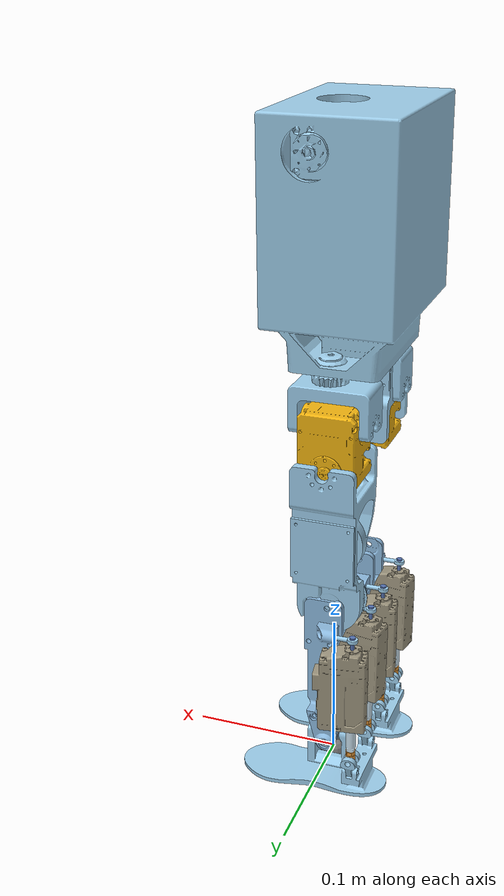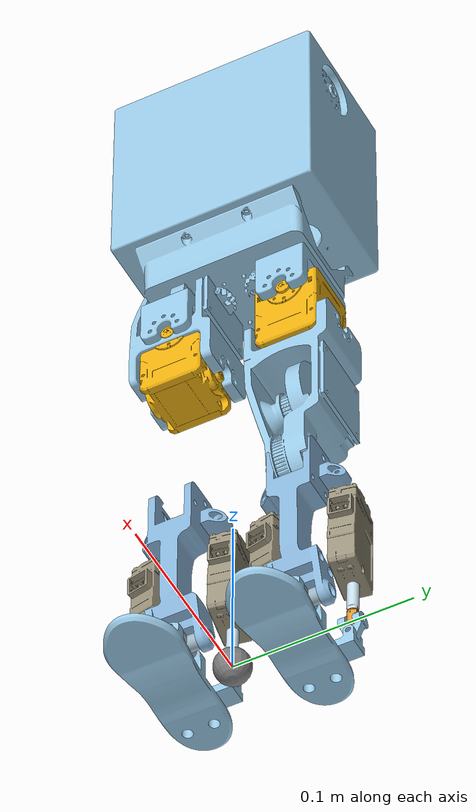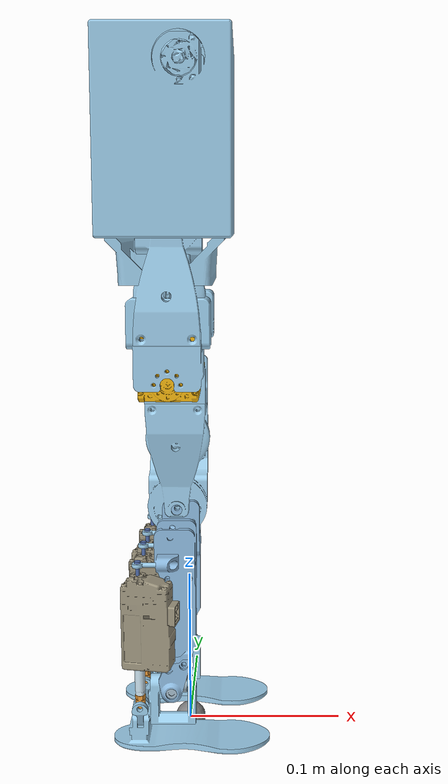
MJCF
<mujoco model="toddlerbot_legs">
  <compiler angle="radian" />
  <asset>
    <mesh name="body_link_visual" file="../assemblies/no_body/meshes/body_link_visual.stl" />
    <mesh name="body_link_collision" file="collisions/body_link_collision.stl" />
    <mesh name="left_hip_yaw_link_visual" file="../assemblies/left_3R+RH5_leg/meshes/left_hip_yaw_link_visual.stl" />
    <mesh name="left_hip_roll_link_visual" file="../assemblies/left_3R+RH5_leg/meshes/left_hip_roll_link_visual.stl" />
    <mesh name="left_hip_roll_link_collision" file="collisions/left_hip_roll_link_collision.stl" />
    <mesh name="left_hip_pitch_link_visual" file="../assemblies/left_3R+RH5_leg/meshes/left_hip_pitch_link_visual.stl" />
    <mesh name="left_hip_pitch_link_collision" file="collisions/left_hip_pitch_link_collision.stl" />
    <mesh name="left_calf_link_visual" file="../assemblies/left_3R+RH5_leg/meshes/left_calf_link_visual.stl" />
    <mesh name="left_calf_link_collision" file="collisions/left_calf_link_collision.stl" />
    <mesh name="left_ank_pitch_link_visual" file="../assemblies/left_3R+RH5_leg/meshes/left_ank_pitch_link_visual.stl" />
    <mesh name="left_ank_roll_link_visual" file="../assemblies/left_3R+RH5_leg/meshes/left_ank_roll_link_visual.stl" />
    <mesh name="left_ank_roll_link_collision" file="../assemblies/left_3R+RH5_leg/meshes/left_ank_roll_link_collision.stl" />
    <mesh name="left_ank_rr_link_visual" file="../assemblies/left_3R+RH5_leg/meshes/left_ank_rr_link_visual.stl" />
    <mesh name="left_12lf_rod_end_visual" file="../assemblies/left_3R+RH5_leg/meshes/left_12lf_rod_end_visual.stl" />
    <mesh name="left_ank_rr_link_2_visual" file="../assemblies/left_3R+RH5_leg/meshes/left_ank_rr_link_2_visual.stl" />
    <mesh name="left_12lf_rod_end_2_visual" file="../assemblies/left_3R+RH5_leg/meshes/left_12lf_rod_end_2_visual.stl" />
    <mesh name="left_ball_joint_container_visual" file="../assemblies/left_3R+RH5_leg/meshes/left_ball_joint_container_visual.stl" />
    <mesh name="left_ball_joint_ball_visual" file="../assemblies/left_3R+RH5_leg/meshes/left_ball_joint_ball_visual.stl" />
    <mesh name="left_12lf_visual" file="../assemblies/left_3R+RH5_leg/meshes/left_12lf_visual.stl" />
    <mesh name="left_12lf_rod_visual" file="../assemblies/left_3R+RH5_leg/meshes/left_12lf_rod_visual.stl" />
    <mesh name="left_ball_joint_container_2_visual" file="../assemblies/left_3R+RH5_leg/meshes/left_ball_joint_container_2_visual.stl" />
    <mesh name="left_ball_joint_ball_2_visual" file="../assemblies/left_3R+RH5_leg/meshes/left_ball_joint_ball_2_visual.stl" />
    <mesh name="left_12lf_2_visual" file="../assemblies/left_3R+RH5_leg/meshes/left_12lf_2_visual.stl" />
    <mesh name="left_12lf_rod_2_visual" file="../assemblies/left_3R+RH5_leg/meshes/left_12lf_rod_2_visual.stl" />
    <mesh name="right_hip_yaw_link_visual" file="../assemblies/right_3R+RH5_leg/meshes/right_hip_yaw_link_visual.stl" />
    <mesh name="right_hip_roll_link_visual" file="../assemblies/right_3R+RH5_leg/meshes/right_hip_roll_link_visual.stl" />
    <mesh name="right_hip_roll_link_collision" file="collisions/right_hip_roll_link_collision.stl" />
    <mesh name="right_hip_pitch_link_visual" file="../assemblies/right_3R+RH5_leg/meshes/right_hip_pitch_link_visual.stl" />
    <mesh name="right_hip_pitch_link_collision" file="collisions/right_hip_pitch_link_collision.stl" />
    <mesh name="right_calf_link_visual" file="../assemblies/right_3R+RH5_leg/meshes/right_calf_link_visual.stl" />
    <mesh name="right_calf_link_collision" file="collisions/right_calf_link_collision.stl" />
    <mesh name="right_ank_pitch_link_visual" file="../assemblies/right_3R+RH5_leg/meshes/right_ank_pitch_link_visual.stl" />
    <mesh name="right_ank_roll_link_visual" file="../assemblies/right_3R+RH5_leg/meshes/right_ank_roll_link_visual.stl" />
    <mesh name="right_ank_roll_link_collision" file="../assemblies/right_3R+RH5_leg/meshes/right_ank_roll_link_collision.stl" />
    <mesh name="right_ank_rr_link_visual" file="../assemblies/right_3R+RH5_leg/meshes/right_ank_rr_link_visual.stl" />
    <mesh name="right_12lf_rod_end_visual" file="../assemblies/right_3R+RH5_leg/meshes/right_12lf_rod_end_visual.stl" />
    <mesh name="right_ank_rr_link_2_visual" file="../assemblies/right_3R+RH5_leg/meshes/right_ank_rr_link_2_visual.stl" />
    <mesh name="right_12lf_rod_end_2_visual" file="../assemblies/right_3R+RH5_leg/meshes/right_12lf_rod_end_2_visual.stl" />
    <mesh name="right_ball_joint_container_visual" file="../assemblies/right_3R+RH5_leg/meshes/right_ball_joint_container_visual.stl" />
    <mesh name="right_ball_joint_ball_visual" file="../assemblies/right_3R+RH5_leg/meshes/right_ball_joint_ball_visual.stl" />
    <mesh name="right_12lf_visual" file="../assemblies/right_3R+RH5_leg/meshes/right_12lf_visual.stl" />
    <mesh name="right_12lf_rod_visual" file="../assemblies/right_3R+RH5_leg/meshes/right_12lf_rod_visual.stl" />
    <mesh name="right_ball_joint_container_2_visual" file="../assemblies/right_3R+RH5_leg/meshes/right_ball_joint_container_2_visual.stl" />
    <mesh name="right_ball_joint_ball_2_visual" file="../assemblies/right_3R+RH5_leg/meshes/right_ball_joint_ball_2_visual.stl" />
    <mesh name="right_12lf_2_visual" file="../assemblies/right_3R+RH5_leg/meshes/right_12lf_2_visual.stl" />
    <mesh name="right_12lf_rod_2_visual" file="../assemblies/right_3R+RH5_leg/meshes/right_12lf_rod_2_visual.stl" />
  </asset>
  <worldbody>
    <site name="imu" size="0.01" pos="0.0 0 0.0" />
    <site name="torso" fromto="0.01 0 0.4 -0.01 0 0.4" type="cylinder" size="0.005 0.005 1" group="3" />
    <geom rgba="0.613972 0.803325 0.915409 1" mesh="body_link_visual" class="visual" />
    <geom rgba="0.613972 0.803325 0.915409 1" mesh="body_link_collision" class="collision" />
    <body name="hip_yaw_link" pos="-0.0094 0.034 0.285" quat="1 0 0 0">
      <inertial pos="0 0 -0.00983905" quat="0 0.707107 0 0.707107" mass="0.00902588" diaginertia="3.87214e-06 3.84085e-06 1.32305e-06" />
      <joint name="left_hip_yaw" pos="0 0 0" axis="0 0 1" limited="true" range="-0.785398 0.785398" damping="1.459" armature="0.0228" frictionloss="0.1143" />
      <geom rgba="0.615686 0.811765 0.929412 1" mesh="left_hip_yaw_link_visual" class="visual" />
      <body name="hip_roll_link" pos="0.019 0 -0.026" quat="0 0.707107 0 0.707107">
        <inertial pos="-0.0119998 -0.000495981 -0.0185041" quat="-0.273471 0.652073 -0.267709 0.654482" mass="0.0980124" diaginertia="2.78674e-05 2.68492e-05 2.02212e-05" />
        <joint name="left_hip_roll" pos="0 0 0" axis="0 0 1" limited="true" range="-0.785398 1.5708" damping="3.122" armature="0.1" frictionloss="0.0002" />
        <geom rgba="0.950187 0.706789 0.0616121 1" mesh="left_hip_roll_link_visual" class="visual" />
        <geom rgba="0.950187 0.706789 0.0616121 1" mesh="left_hip_roll_link_collision" class="collision" />
        <body name="left_hip_pitch_link" pos="-0.024 -0.019 -0.019" quat="0.5 -0.5 0.5 0.5">
          <inertial pos="-0.000219203 0.0528672 0.0146752" quat="0.675957 0.69839 0.172666 -0.15975" mass="0.0936117" diaginertia="6.26646e-05 6.22569e-05 2.15273e-05" />
          <joint name="left_hip_pitch" pos="0 0 0" axis="0 0 1" limited="true" range="-1.5708 1.5708" damping="1.286" armature="0.0032" frictionloss="0.0" />
          <geom rgba="0.616541 0.807279 0.921723 1" mesh="left_hip_pitch_link_visual" class="visual" />
          <geom rgba="0.616541 0.807279 0.921723 1" mesh="left_hip_pitch_link_collision" class="collision" />
          <body name="left_calf_link" pos="0 0.096 0.0274" quat="0 1 0 0">
            <inertial pos="-0.0038993 -0.0424193 0.00818649" quat="0.707628 0.706515 -0.00993164 -0.00118734" mass="0.0157824" diaginertia="1.47483e-05 1.4045e-05 1.89387e-06" />
            <joint name="left_knee" pos="0 0 0" axis="0 0 1" limited="true" range="0 1.5708" damping="1.142" armature="0.0" frictionloss="0.0319" />
            <geom rgba="0.551854 0.729722 0.876657 1" mesh="left_calf_link_visual" class="visual" />
            <geom rgba="0.551854 0.729722 0.876657 1" mesh="left_calf_link_collision" class="collision" />
            <body name="ank_pitch_link" pos="0 -0.1 -0.0062" quat="0 0.707107 -0.707107 0">
              <inertial pos="4.02697e-08 0.000595283 -0.0145999" quat="1 0 -2.35914e-06 0" mass="0.00422384" diaginertia="4.37053e-07 3.97827e-07 8.88586e-08" />
              <joint name="left_ank_pitch" pos="0 0 0" axis="0 0 1" limited="true" range="-0.785398 0.959931" damping="0.523" armature="0.0115" frictionloss="0.0005" />
              <geom rgba="0.631892 0.726687 0.783564 1" mesh="left_ank_pitch_link_visual" class="visual" />
              <body name="ank_roll_link" pos="0 0.0015 -0.0146" quat="0.5 -0.5 -0.5 -0.5">
                <inertial pos="-3.28026e-07 0.0289226 0.00175005" quat="0.996871 -0.0790494 6.17315e-06 5.36738e-05" mass="0.013975" diaginertia="1.02121e-05 9.92043e-06 2.55434e-06" />
                <joint name="left_ank_roll" pos="0 0 0" axis="0 0 1" limited="true" range="-0.785398 0.785398" damping="0.583" armature="0.0158" frictionloss="0.0003" />
                <geom rgba="0.615686 0.811765 0.929412 1" mesh="left_ank_roll_link_visual" class="visual" />
                <geom rgba="0.615686 0.811765 0.929412 1" mesh="left_ank_roll_link_collision" class="collision" />
                <body name="ank_rr_link" pos="-0.018 0.016 -0.0206" quat="0.999956 0 0 -0.00938949">
                  <inertial pos="0 -0.00614477 0" quat="0.5 0.5 -0.5 0.5" mass="0.000425071" diaginertia="1.25044e-08 8.78432e-09 8.03017e-09" />
                  <joint name="left_ank_R11" pos="0 0 0" axis="0 0 1" limited="true" range="-1.5708 1.5708" />
                  <geom rgba="0.615686 0.811765 0.929412 1" mesh="left_ank_rr_link_visual" class="visual" />
                  <body name="12lf_rod_end" pos="0 -0.01 0" quat="0.707105 0.00154912 -0.707105 -0.00154912">
                    <inertial pos="-4.47352e-11 -0.00384222 6.43842e-06" quat="0.500199 0.499801 -0.499801 0.500199" mass="0.000854205" diaginertia="1.27035e-08 1.1841e-08 3.35496e-09" />
                    <joint name="left_ank_R21" pos="0 0 0" axis="0 0 1" limited="true" range="-1.5708 1.5708" />
                    <geom rgba="0.927718 0.610493 0.218477 1" mesh="left_12lf_rod_end_visual" class="visual" />
                  </body>
                </body>
                <body name="ank_rr_link_2" pos="0.018 0.016 -0.0206" quat="0 0.00933097 -0.999956 0">
                  <inertial pos="0 -0.00614477 0" quat="0.5 0.5 -0.5 0.5" mass="0.000425071" diaginertia="1.25044e-08 8.78432e-09 8.03017e-09" />
                  <joint name="left_ank_R12" pos="0 0 0" axis="0 0 1" limited="true" range="-1.5708 1.5708" />
                  <geom rgba="0.615686 0.811765 0.929412 1" mesh="left_ank_rr_link_2_visual" class="visual" />
                  <body name="12lf_rod_end_2" pos="0 -0.01 0" quat="0.707105 -0.00154102 -0.707105 0.00154102">
                    <inertial pos="-4.47352e-11 -0.00384222 6.43842e-06" quat="0.500199 0.499801 -0.499801 0.500199" mass="0.000854205" diaginertia="1.27035e-08 1.1841e-08 3.35496e-09" />
                    <joint name="left_ank_R22" pos="0 0 0" axis="0 0 1" limited="true" range="-1.5708 1.5708" />
                    <geom rgba="0.927718 0.610493 0.218477 1" mesh="left_12lf_rod_end_2_visual" class="visual" />
                  </body>
                </body>
              </body>
            </body>
            <body name="ball_joint_container" pos="0.008 -0.015 0.0283" quat="0.00663937 -0.707076 -0.00663937 0.707076">
              <inertial pos="0 0 -0.00971253" quat="0.707107 0 0 0.707107" mass="4.80374e-05" diaginertia="8.47542e-10 7.18655e-10 1.86253e-10" />
              <joint name="left_ank_B11" pos="0 0 0" axis="0 0 1" limited="true" range="-0.785398 0.785398" />
              <geom rgba="0.615686 0.811765 0.929412 1" mesh="left_ball_joint_container_visual" class="visual" />
              <body name="ball_joint_ball" pos="0 0 -0.0115" quat="0.00154912 -0.707105 0.00154912 -0.707105">
                <inertial pos="0 -0.00103087 0" quat="0.707107 0.707107 0 0" mass="4.40538e-05" diaginertia="3.1285e-10 3.12853e-10 6.25696e-11" />
                <joint name="left_ank_B21" pos="0 0 0" axis="0 0 1" limited="true" range="-0.785398 0.785398" />
                <geom rgba="0.32913 0.443105 0.692049 1" mesh="left_ball_joint_ball_visual" class="visual" />
                <body name="12lf" pos="0 -0.00643875 0" quat="0.70458 -0.70458 0.0597268 0.0597268">
                  <inertial pos="0.00490842 -0.000138024 -0.029947" quat="0.709913 0.00132323 0.0043477 0.704274" mass="0.0447822" diaginertia="1.81889e-05 1.52606e-05 5.14874e-06" />
                  <joint name="left_ank_B31" pos="0 0 0" axis="0 0 1" limited="true" range="-0.785398 0.785398" />
                  <geom rgba="0.620044 0.588367 0.498971 1" mesh="left_12lf_visual" class="visual" />
                  <body name="12lf_rod" pos="2.27221e-06 0 -0.07478" quat="0 -0.452653 0.891687 0">
                    <inertial pos="-6.32221e-07 4.69333e-07 -0.0128934" quat="1 -2.00488e-05 -2.69482e-05 -5.4028e-10" mass="0.00250883" diaginertia="2.69445e-07 2.69445e-07 1.78098e-08" />
                    <joint name="left_ank_act1" pos="0 0 0" axis="0 0 1" type="slide" limited="true" range="0 0.04" />
                    <geom rgba="0.802503 0.893406 0.944918 1" mesh="left_12lf_rod_visual" class="visual" />
                  </body>
                </body>
              </body>
            </body>
            <body name="ball_joint_container_2" pos="0.008 -0.015 -0.0115" quat="0.707076 -0.00659799 -0.707076 0.00659799">
              <inertial pos="0 0 -0.00971253" quat="0.707107 0 0 0.707107" mass="4.80374e-05" diaginertia="8.47542e-10 7.18655e-10 1.86253e-10" />
              <joint name="left_ank_B12" pos="0 0 0" axis="0 0 1" limited="true" range="-0.785398 0.785398" />
              <geom rgba="0.615686 0.811765 0.929412 1" mesh="left_ball_joint_container_2_visual" class="visual" />
              <body name="ball_joint_ball_2" pos="0 0 -0.0115" quat="0.707105 -0.00154102 -0.707105 0.00154102">
                <inertial pos="0 -0.00103087 0" quat="0.707107 0.707107 0 0" mass="4.40538e-05" diaginertia="3.1285e-10 3.12853e-10 6.25696e-11" />
                <joint name="left_ank_B22" pos="0 0 0" axis="0 0 1" limited="true" range="-0.785398 0.785398" />
                <geom rgba="0.32913 0.443105 0.692049 1" mesh="left_ball_joint_ball_2_visual" class="visual" />
                <body name="12lf_2" pos="0 -0.00643875 0" quat="0.704247 -0.704247 -0.0635296 -0.0635296">
                  <inertial pos="0.00490842 -0.000138024 -0.029947" quat="0.709913 0.00132323 0.0043477 0.704274" mass="0.0447822" diaginertia="1.81889e-05 1.52606e-05 5.14874e-06" />
                  <joint name="left_ank_B32" pos="0 0 0" axis="0 0 1" limited="true" range="-0.785398 0.785398" />
                  <geom rgba="0.620044 0.588367 0.498971 1" mesh="left_12lf_2_visual" class="visual" />
                  <body name="12lf_rod_2" pos="2.27221e-06 0 -0.07478" quat="0 -0.452653 0.891687 0">
                    <inertial pos="-6.32221e-07 4.69333e-07 -0.0128934" quat="1 -2.00488e-05 -2.69482e-05 -5.4028e-10" mass="0.00250883" diaginertia="2.69445e-07 2.69445e-07 1.78098e-08" />
                    <joint name="left_ank_act2" pos="0 0 0" axis="0 0 1" type="slide" limited="true" range="0 0.04" />
                    <geom rgba="0.802503 0.893406 0.944918 1" mesh="left_12lf_rod_2_visual" class="visual" />
                  </body>
                </body>
              </body>
            </body>
          </body>
        </body>
      </body>
    </body>
    <body name="hip_yaw_link_2" pos="-0.0094 -0.034 0.285" quat="1 0 0 0">
      <inertial pos="0 0 -0.00983905" quat="0 0.707107 0 0.707107" mass="0.00902588" diaginertia="3.87214e-06 3.84085e-06 1.32305e-06" />
      <joint name="right_hip_yaw" pos="0 0 0" axis="0 0 1" limited="true" range="-0.785398 0.785398" damping="1.459" armature="0.0228" frictionloss="0.1143" />
      <geom rgba="0.615686 0.811765 0.929412 1" mesh="right_hip_yaw_link_visual" class="visual" />
      <body name="hip_roll_link_2" pos="0.019 0 -0.026" quat="0 0.707107 0 0.707107">
        <inertial pos="-0.0119998 -0.000495981 -0.0185041" quat="-0.273471 0.652073 -0.267709 0.654482" mass="0.0980124" diaginertia="2.78674e-05 2.68492e-05 2.02212e-05" />
        <joint name="right_hip_roll" pos="0 0 0" axis="0 0 1" limited="true" range="-1.5708 0.785398" damping="3.122" armature="0.1" frictionloss="0.0002" />
        <geom rgba="0.950187 0.706789 0.0616121 1" mesh="right_hip_roll_link_visual" class="visual" />
        <geom rgba="0.950187 0.706789 0.0616121 1" mesh="right_hip_roll_link_collision" class="collision" />
        <body name="right_hip_pitch_link" pos="-0.024 -0.019 -0.019" quat="0.5 -0.5 -0.5 -0.5">
          <inertial pos="-1.30337e-05 -0.0528672 0.0233248" quat="0.694519 0.719422 -0.00407443 0.00772147" mass="0.0936117" diaginertia="6.25764e-05 6.23465e-05 2.15349e-05" />
          <joint name="right_hip_pitch" pos="0 0 0" axis="0 0 1" limited="true" range="-1.5708 1.5708" damping="1.286" armature="0.0032" frictionloss="0.0" />
          <geom rgba="0.616541 0.807279 0.921723 1" mesh="right_hip_pitch_link_visual" class="visual" />
          <geom rgba="0.616541 0.807279 0.921723 1" mesh="right_hip_pitch_link_collision" class="collision" />
          <body name="right_calf_link" pos="0 -0.096 0.0106" quat="0 0 0 1">
            <inertial pos="-0.00389996 0.0424094 0.00818387" quat="0.706581 0.70756 0.0011042 0.0100571" mass="0.0157797" diaginertia="1.47387e-05 1.40359e-05 1.89319e-06" />
            <joint name="right_knee" pos="0 0 0" axis="0 0 1" limited="true" range="-1.5708 0" damping="1.142" armature="0.0" frictionloss="0.0319" />
            <geom rgba="0.551838 0.729737 0.876696 1" mesh="right_calf_link_visual" class="visual" />
            <geom rgba="0.551838 0.729737 0.876696 1" mesh="right_calf_link_collision" class="collision" />
            <body name="ank_pitch_link_2" pos="0 0.1 -0.0062" quat="0 -0.707107 0.707107 0">
              <inertial pos="4.02697e-08 0.000595283 -0.0145999" quat="1 0 -2.35914e-06 0" mass="0.00422384" diaginertia="4.37053e-07 3.97827e-07 8.88586e-08" />
              <joint name="right_ank_pitch" pos="0 0 0" axis="0 0 1" limited="true" range="-0.785398 0.959931" damping="0.523" armature="0.0115" frictionloss="0.0005" />
              <geom rgba="0.631892 0.726687 0.783564 1" mesh="right_ank_pitch_link_visual" class="visual" />
              <body name="ank_roll_link_2" pos="0 0.0015 -0.0146" quat="0.5 -0.5 0.5 0.5">
                <inertial pos="-1.72813e-07 0.0289226 0.00175013" quat="0.996871 -0.07905 7.3645e-06 4.94885e-05" mass="0.013975" diaginertia="1.02121e-05 9.92044e-06 2.55435e-06" />
                <joint name="right_ank_roll" pos="0 0 0" axis="0 0 1" limited="true" range="-0.785398 0.785398" damping="0.583" armature="0.0158" frictionloss="0.0003" />
                <geom rgba="0.615686 0.811765 0.929412 1" mesh="right_ank_roll_link_visual" class="visual" />
                <geom rgba="0.615686 0.811765 0.929412 1" mesh="right_ank_roll_link_collision" class="collision" />
                <body name="ank_rr_link_3" pos="-0.018 0.016 -0.0206" quat="0.999956 0 0 -0.00938949">
                  <inertial pos="0 -0.00614477 0" quat="0.5 0.5 -0.5 0.5" mass="0.000425071" diaginertia="1.25044e-08 8.78432e-09 8.03017e-09" />
                  <joint name="right_ank_R11" pos="0 0 0" axis="0 0 1" limited="true" range="-1.5708 1.5708" />
                  <geom rgba="0.615686 0.811765 0.929412 1" mesh="right_ank_rr_link_visual" class="visual" />
                  <body name="12lf_rod_end_3" pos="0 -0.01 0" quat="0.707105 0.00154912 -0.707105 -0.00154912">
                    <inertial pos="-4.47352e-11 -0.00384222 6.43842e-06" quat="0.500199 0.499801 -0.499801 0.500199" mass="0.000854205" diaginertia="1.27035e-08 1.1841e-08 3.35496e-09" />
                    <joint name="right_ank_R21" pos="0 0 0" axis="0 0 1" limited="true" range="-1.5708 1.5708" />
                    <geom rgba="0.927718 0.610493 0.218477 1" mesh="right_12lf_rod_end_visual" class="visual" />
                  </body>
                </body>
                <body name="ank_rr_link_4" pos="0.018 0.016 -0.0206" quat="0 -0.00933097 0.999956 0">
                  <inertial pos="0 -0.00614477 0" quat="0.5 0.5 -0.5 0.5" mass="0.000425071" diaginertia="1.25044e-08 8.78432e-09 8.03017e-09" />
                  <joint name="right_ank_R12" pos="0 0 0" axis="0 0 1" limited="true" range="-1.5708 1.5708" />
                  <geom rgba="0.615686 0.811765 0.929412 1" mesh="right_ank_rr_link_2_visual" class="visual" />
                  <body name="12lf_rod_end_4" pos="0 -0.01 0" quat="0.707105 -0.00154102 -0.707105 0.00154102">
                    <inertial pos="-4.47352e-11 -0.00384222 6.43842e-06" quat="0.500199 0.499801 -0.499801 0.500199" mass="0.000854205" diaginertia="1.27035e-08 1.1841e-08 3.35496e-09" />
                    <joint name="right_ank_R22" pos="0 0 0" axis="0 0 1" limited="true" range="-1.5708 1.5708" />
                    <geom rgba="0.927718 0.610493 0.218477 1" mesh="right_12lf_rod_end_2_visual" class="visual" />
                  </body>
                </body>
              </body>
            </body>
            <body name="ball_joint_container_3" pos="0.008 0.015 -0.0115" quat="0.707076 0.00663937 -0.707076 -0.00663937">
              <inertial pos="0 0 -0.00971253" quat="0.707107 0 0 0.707107" mass="4.80374e-05" diaginertia="8.47542e-10 7.18655e-10 1.86253e-10" />
              <joint name="right_ank_B11" pos="0 0 0" axis="0 0 1" limited="true" range="-0.785398 0.785398" />
              <geom rgba="0.615686 0.811765 0.929412 1" mesh="right_ball_joint_container_visual" class="visual" />
              <body name="ball_joint_ball_3" pos="0 0 -0.0115" quat="0.00154912 -0.707105 0.00154912 -0.707105">
                <inertial pos="0 -0.00103087 0" quat="0.707107 0.707107 0 0" mass="4.40538e-05" diaginertia="3.1285e-10 3.12853e-10 6.25696e-11" />
                <joint name="right_ank_B21" pos="0 0 0" axis="0 0 1" limited="true" range="-0.785398 0.785398" />
                <geom rgba="0.32913 0.443105 0.692049 1" mesh="right_ball_joint_ball_visual" class="visual" />
                <body name="12lf_3" pos="0 -0.00643875 0" quat="0.70458 -0.70458 0.0597268 0.0597268">
                  <inertial pos="0.00490842 -0.000138024 -0.029947" quat="0.709913 0.00132323 0.0043477 0.704274" mass="0.0447822" diaginertia="1.81889e-05 1.52606e-05 5.14874e-06" />
                  <joint name="right_ank_B31" pos="0 0 0" axis="0 0 1" limited="true" range="-0.785398 0.785398" />
                  <geom rgba="0.620044 0.588367 0.498971 1" mesh="right_12lf_visual" class="visual" />
                  <body name="12lf_rod_3" pos="2.27221e-06 0 -0.07478" quat="0 -0.452653 0.891687 0">
                    <inertial pos="-6.32221e-07 4.69333e-07 -0.0128934" quat="1 -2.00488e-05 -2.69482e-05 -5.4028e-10" mass="0.00250883" diaginertia="2.69445e-07 2.69445e-07 1.78098e-08" />
                    <joint name="right_ank_act1" pos="0 0 0" axis="0 0 1" type="slide" limited="true" range="0 0.04" />
                    <geom rgba="0.802503 0.893406 0.944918 1" mesh="right_12lf_rod_visual" class="visual" />
                  </body>
                </body>
              </body>
            </body>
            <body name="ball_joint_container_4" pos="0.008 0.015 0.0283" quat="0.707076 -0.00659799 -0.707076 0.00659799">
              <inertial pos="0 0 -0.00971253" quat="0.707107 0 0 0.707107" mass="4.80374e-05" diaginertia="8.47542e-10 7.18655e-10 1.86253e-10" />
              <joint name="right_ank_B12" pos="0 0 0" axis="0 0 1" limited="true" range="-0.785398 0.785398" />
              <geom rgba="0.615686 0.811765 0.929412 1" mesh="right_ball_joint_container_2_visual" class="visual" />
              <body name="ball_joint_ball_4" pos="0 0 -0.0115" quat="0.00154102 -0.707105 0.00154102 -0.707105">
                <inertial pos="0 -0.00103087 0" quat="0.707107 0.707107 0 0" mass="4.40538e-05" diaginertia="3.1285e-10 3.12853e-10 6.25696e-11" />
                <joint name="right_ank_B22" pos="0 0 0" axis="0 0 1" limited="true" range="-0.785398 0.785398" />
                <geom rgba="0.32913 0.443105 0.692049 1" mesh="right_ball_joint_ball_2_visual" class="visual" />
                <body name="12lf_4" pos="0 -0.00643875 0" quat="0.704247 -0.704247 -0.0635296 -0.0635296">
                  <inertial pos="0.00490842 -0.000138024 -0.029947" quat="0.709913 0.00132323 0.0043477 0.704274" mass="0.0447822" diaginertia="1.81889e-05 1.52606e-05 5.14874e-06" />
                  <joint name="right_ank_B32" pos="0 0 0" axis="0 0 1" limited="true" range="-0.785398 0.785398" />
                  <geom rgba="0.620044 0.588367 0.498971 1" mesh="right_12lf_2_visual" class="visual" />
                  <body name="12lf_rod_4" pos="2.27221e-06 0 -0.07478" quat="0 0.452653 -0.891687 0">
                    <inertial pos="-6.32221e-07 4.69333e-07 -0.0128934" quat="1 -2.00488e-05 -2.69482e-05 -5.4028e-10" mass="0.00250883" diaginertia="2.69445e-07 2.69445e-07 1.78098e-08" />
                    <joint name="right_ank_act2" pos="0 0 0" axis="0 0 1" type="slide" limited="true" range="0 0.04" />
                    <geom rgba="0.802503 0.893406 0.944918 1" mesh="right_12lf_rod_2_visual" class="visual" />
                  </body>
                </body>
              </body>
            </body>
          </body>
        </body>
      </body>
    </body>
  </worldbody>
  <sensor>
    <framequat name="orientation" objtype="site" noise="0.001" objname="imu" />
    <framepos name="position" objtype="site" noise="0.001" objname="imu" />
    <gyro name="angular_velocity" site="imu" noise="0.005" cutoff="34.9" />
    <velocimeter name="linear_velocity" site="imu" noise="0.001" cutoff="30" />
    <accelerometer name="linear_acceleration" site="imu" noise="0.005" cutoff="157" />
    <magnetometer name="magnetometer" site="imu" />
  </sensor>
  <contact>
    <exclude body1="hip_yaw_link" body2="hip_roll_link" />
    <exclude body1="hip_yaw_link" body2="left_hip_pitch_link" />
    <exclude body1="hip_yaw_link" body2="left_calf_link" />
    <exclude body1="hip_yaw_link" body2="ank_pitch_link" />
    <exclude body1="hip_yaw_link" body2="ank_roll_link" />
    <exclude body1="hip_yaw_link" body2="ank_rr_link" />
    <exclude body1="hip_yaw_link" body2="12lf_rod_end" />
    <exclude body1="hip_yaw_link" body2="ank_rr_link_2" />
    <exclude body1="hip_yaw_link" body2="12lf_rod_end_2" />
    <exclude body1="hip_yaw_link" body2="ball_joint_container" />
    <exclude body1="hip_yaw_link" body2="ball_joint_ball" />
    <exclude body1="hip_yaw_link" body2="12lf" />
    <exclude body1="hip_yaw_link" body2="12lf_rod" />
    <exclude body1="hip_yaw_link" body2="ball_joint_container_2" />
    <exclude body1="hip_yaw_link" body2="ball_joint_ball_2" />
    <exclude body1="hip_yaw_link" body2="12lf_2" />
    <exclude body1="hip_yaw_link" body2="12lf_rod_2" />
    <exclude body1="hip_yaw_link" body2="hip_yaw_link_2" />
    <exclude body1="hip_yaw_link" body2="hip_roll_link_2" />
    <exclude body1="hip_yaw_link" body2="right_hip_pitch_link" />
    <exclude body1="hip_yaw_link" body2="right_calf_link" />
    <exclude body1="hip_yaw_link" body2="ank_pitch_link_2" />
    <exclude body1="hip_yaw_link" body2="ank_roll_link_2" />
    <exclude body1="hip_yaw_link" body2="ank_rr_link_3" />
    <exclude body1="hip_yaw_link" body2="12lf_rod_end_3" />
    <exclude body1="hip_yaw_link" body2="ank_rr_link_4" />
    <exclude body1="hip_yaw_link" body2="12lf_rod_end_4" />
    <exclude body1="hip_yaw_link" body2="ball_joint_container_3" />
    <exclude body1="hip_yaw_link" body2="ball_joint_ball_3" />
    <exclude body1="hip_yaw_link" body2="12lf_3" />
    <exclude body1="hip_yaw_link" body2="12lf_rod_3" />
    <exclude body1="hip_yaw_link" body2="ball_joint_container_4" />
    <exclude body1="hip_yaw_link" body2="ball_joint_ball_4" />
    <exclude body1="hip_yaw_link" body2="12lf_4" />
    <exclude body1="hip_yaw_link" body2="12lf_rod_4" />
    <exclude body1="hip_roll_link" body2="hip_yaw_link" />
    <exclude body1="hip_roll_link" body2="left_hip_pitch_link" />
    <exclude body1="hip_roll_link" body2="left_calf_link" />
    <exclude body1="hip_roll_link" body2="ank_pitch_link" />
    <exclude body1="hip_roll_link" body2="ank_roll_link" />
    <exclude body1="hip_roll_link" body2="ank_rr_link" />
    <exclude body1="hip_roll_link" body2="12lf_rod_end" />
    <exclude body1="hip_roll_link" body2="ank_rr_link_2" />
    <exclude body1="hip_roll_link" body2="12lf_rod_end_2" />
    <exclude body1="hip_roll_link" body2="ball_joint_container" />
    <exclude body1="hip_roll_link" body2="ball_joint_ball" />
    <exclude body1="hip_roll_link" body2="12lf" />
    <exclude body1="hip_roll_link" body2="12lf_rod" />
    <exclude body1="hip_roll_link" body2="ball_joint_container_2" />
    <exclude body1="hip_roll_link" body2="ball_joint_ball_2" />
    <exclude body1="hip_roll_link" body2="12lf_2" />
    <exclude body1="hip_roll_link" body2="12lf_rod_2" />
    <exclude body1="hip_roll_link" body2="hip_yaw_link_2" />
    <exclude body1="hip_roll_link" body2="hip_roll_link_2" />
    <exclude body1="hip_roll_link" body2="right_hip_pitch_link" />
    <exclude body1="hip_roll_link" body2="right_calf_link" />
    <exclude body1="hip_roll_link" body2="ank_pitch_link_2" />
    <exclude body1="hip_roll_link" body2="ank_roll_link_2" />
    <exclude body1="hip_roll_link" body2="ank_rr_link_3" />
    <exclude body1="hip_roll_link" body2="12lf_rod_end_3" />
    <exclude body1="hip_roll_link" body2="ank_rr_link_4" />
    <exclude body1="hip_roll_link" body2="12lf_rod_end_4" />
    <exclude body1="hip_roll_link" body2="ball_joint_container_3" />
    <exclude body1="hip_roll_link" body2="ball_joint_ball_3" />
    <exclude body1="hip_roll_link" body2="12lf_3" />
    <exclude body1="hip_roll_link" body2="12lf_rod_3" />
    <exclude body1="hip_roll_link" body2="ball_joint_container_4" />
    <exclude body1="hip_roll_link" body2="ball_joint_ball_4" />
    <exclude body1="hip_roll_link" body2="12lf_4" />
    <exclude body1="hip_roll_link" body2="12lf_rod_4" />
    <exclude body1="left_hip_pitch_link" body2="hip_yaw_link" />
    <exclude body1="left_hip_pitch_link" body2="hip_roll_link" />
    <exclude body1="left_hip_pitch_link" body2="left_calf_link" />
    <exclude body1="left_hip_pitch_link" body2="ank_pitch_link" />
    <exclude body1="left_hip_pitch_link" body2="ank_roll_link" />
    <exclude body1="left_hip_pitch_link" body2="ank_rr_link" />
    <exclude body1="left_hip_pitch_link" body2="12lf_rod_end" />
    <exclude body1="left_hip_pitch_link" body2="ank_rr_link_2" />
    <exclude body1="left_hip_pitch_link" body2="12lf_rod_end_2" />
    <exclude body1="left_hip_pitch_link" body2="ball_joint_container" />
    <exclude body1="left_hip_pitch_link" body2="ball_joint_ball" />
    <exclude body1="left_hip_pitch_link" body2="12lf" />
    <exclude body1="left_hip_pitch_link" body2="12lf_rod" />
    <exclude body1="left_hip_pitch_link" body2="ball_joint_container_2" />
    <exclude body1="left_hip_pitch_link" body2="ball_joint_ball_2" />
    <exclude body1="left_hip_pitch_link" body2="12lf_2" />
    <exclude body1="left_hip_pitch_link" body2="12lf_rod_2" />
    <exclude body1="left_hip_pitch_link" body2="hip_yaw_link_2" />
    <exclude body1="left_hip_pitch_link" body2="hip_roll_link_2" />
    <exclude body1="left_hip_pitch_link" body2="right_hip_pitch_link" />
    <exclude body1="left_hip_pitch_link" body2="right_calf_link" />
    <exclude body1="left_hip_pitch_link" body2="ank_pitch_link_2" />
    <exclude body1="left_hip_pitch_link" body2="ank_roll_link_2" />
    <exclude body1="left_hip_pitch_link" body2="ank_rr_link_3" />
    <exclude body1="left_hip_pitch_link" body2="12lf_rod_end_3" />
    <exclude body1="left_hip_pitch_link" body2="ank_rr_link_4" />
    <exclude body1="left_hip_pitch_link" body2="12lf_rod_end_4" />
    <exclude body1="left_hip_pitch_link" body2="ball_joint_container_3" />
    <exclude body1="left_hip_pitch_link" body2="ball_joint_ball_3" />
    <exclude body1="left_hip_pitch_link" body2="12lf_3" />
    <exclude body1="left_hip_pitch_link" body2="12lf_rod_3" />
    <exclude body1="left_hip_pitch_link" body2="ball_joint_container_4" />
    <exclude body1="left_hip_pitch_link" body2="ball_joint_ball_4" />
    <exclude body1="left_hip_pitch_link" body2="12lf_4" />
    <exclude body1="left_hip_pitch_link" body2="12lf_rod_4" />
    <exclude body1="left_calf_link" body2="hip_yaw_link" />
    <exclude body1="left_calf_link" body2="hip_roll_link" />
    <exclude body1="left_calf_link" body2="left_hip_pitch_link" />
    <exclude body1="left_calf_link" body2="ank_pitch_link" />
    <exclude body1="left_calf_link" body2="ank_roll_link" />
    <exclude body1="left_calf_link" body2="ank_rr_link" />
    <exclude body1="left_calf_link" body2="12lf_rod_end" />
    <exclude body1="left_calf_link" body2="ank_rr_link_2" />
    <exclude body1="left_calf_link" body2="12lf_rod_end_2" />
    <exclude body1="left_calf_link" body2="ball_joint_container" />
    <exclude body1="left_calf_link" body2="ball_joint_ball" />
    <exclude body1="left_calf_link" body2="12lf" />
    <exclude body1="left_calf_link" body2="12lf_rod" />
    <exclude body1="left_calf_link" body2="ball_joint_container_2" />
    <exclude body1="left_calf_link" body2="ball_joint_ball_2" />
    <exclude body1="left_calf_link" body2="12lf_2" />
    <exclude body1="left_calf_link" body2="12lf_rod_2" />
    <exclude body1="left_calf_link" body2="hip_yaw_link_2" />
    <exclude body1="left_calf_link" body2="hip_roll_link_2" />
    <exclude body1="left_calf_link" body2="right_hip_pitch_link" />
    <exclude body1="left_calf_link" body2="right_calf_link" />
    <exclude body1="left_calf_link" body2="ank_pitch_link_2" />
    <exclude body1="left_calf_link" body2="ank_roll_link_2" />
    <exclude body1="left_calf_link" body2="ank_rr_link_3" />
    <exclude body1="left_calf_link" body2="12lf_rod_end_3" />
    <exclude body1="left_calf_link" body2="ank_rr_link_4" />
    <exclude body1="left_calf_link" body2="12lf_rod_end_4" />
    <exclude body1="left_calf_link" body2="ball_joint_container_3" />
    <exclude body1="left_calf_link" body2="ball_joint_ball_3" />
    <exclude body1="left_calf_link" body2="12lf_3" />
    <exclude body1="left_calf_link" body2="12lf_rod_3" />
    <exclude body1="left_calf_link" body2="ball_joint_container_4" />
    <exclude body1="left_calf_link" body2="ball_joint_ball_4" />
    <exclude body1="left_calf_link" body2="12lf_4" />
    <exclude body1="left_calf_link" body2="12lf_rod_4" />
    <exclude body1="ank_pitch_link" body2="hip_yaw_link" />
    <exclude body1="ank_pitch_link" body2="hip_roll_link" />
    <exclude body1="ank_pitch_link" body2="left_hip_pitch_link" />
    <exclude body1="ank_pitch_link" body2="left_calf_link" />
    <exclude body1="ank_pitch_link" body2="ank_roll_link" />
    <exclude body1="ank_pitch_link" body2="ank_rr_link" />
    <exclude body1="ank_pitch_link" body2="12lf_rod_end" />
    <exclude body1="ank_pitch_link" body2="ank_rr_link_2" />
    <exclude body1="ank_pitch_link" body2="12lf_rod_end_2" />
    <exclude body1="ank_pitch_link" body2="ball_joint_container" />
    <exclude body1="ank_pitch_link" body2="ball_joint_ball" />
    <exclude body1="ank_pitch_link" body2="12lf" />
    <exclude body1="ank_pitch_link" body2="12lf_rod" />
    <exclude body1="ank_pitch_link" body2="ball_joint_container_2" />
    <exclude body1="ank_pitch_link" body2="ball_joint_ball_2" />
    <exclude body1="ank_pitch_link" body2="12lf_2" />
    <exclude body1="ank_pitch_link" body2="12lf_rod_2" />
    <exclude body1="ank_pitch_link" body2="hip_yaw_link_2" />
    <exclude body1="ank_pitch_link" body2="hip_roll_link_2" />
    <exclude body1="ank_pitch_link" body2="right_hip_pitch_link" />
    <exclude body1="ank_pitch_link" body2="right_calf_link" />
    <exclude body1="ank_pitch_link" body2="ank_pitch_link_2" />
    <exclude body1="ank_pitch_link" body2="ank_roll_link_2" />
    <exclude body1="ank_pitch_link" body2="ank_rr_link_3" />
    <exclude body1="ank_pitch_link" body2="12lf_rod_end_3" />
    <exclude body1="ank_pitch_link" body2="ank_rr_link_4" />
    <exclude body1="ank_pitch_link" body2="12lf_rod_end_4" />
    <exclude body1="ank_pitch_link" body2="ball_joint_container_3" />
    <exclude body1="ank_pitch_link" body2="ball_joint_ball_3" />
    <exclude body1="ank_pitch_link" body2="12lf_3" />
    <exclude body1="ank_pitch_link" body2="12lf_rod_3" />
    <exclude body1="ank_pitch_link" body2="ball_joint_container_4" />
    <exclude body1="ank_pitch_link" body2="ball_joint_ball_4" />
    <exclude body1="ank_pitch_link" body2="12lf_4" />
    <exclude body1="ank_pitch_link" body2="12lf_rod_4" />
    <exclude body1="ank_roll_link" body2="hip_yaw_link" />
    <exclude body1="ank_roll_link" body2="hip_roll_link" />
    <exclude body1="ank_roll_link" body2="left_hip_pitch_link" />
    <exclude body1="ank_roll_link" body2="left_calf_link" />
    <exclude body1="ank_roll_link" body2="ank_pitch_link" />
    <exclude body1="ank_roll_link" body2="ank_rr_link" />
    <exclude body1="ank_roll_link" body2="12lf_rod_end" />
    <exclude body1="ank_roll_link" body2="ank_rr_link_2" />
    <exclude body1="ank_roll_link" body2="12lf_rod_end_2" />
    <exclude body1="ank_roll_link" body2="ball_joint_container" />
    <exclude body1="ank_roll_link" body2="ball_joint_ball" />
    <exclude body1="ank_roll_link" body2="12lf" />
    <exclude body1="ank_roll_link" body2="12lf_rod" />
    <exclude body1="ank_roll_link" body2="ball_joint_container_2" />
    <exclude body1="ank_roll_link" body2="ball_joint_ball_2" />
    <exclude body1="ank_roll_link" body2="12lf_2" />
    <exclude body1="ank_roll_link" body2="12lf_rod_2" />
    <exclude body1="ank_roll_link" body2="hip_yaw_link_2" />
    <exclude body1="ank_roll_link" body2="hip_roll_link_2" />
    <exclude body1="ank_roll_link" body2="right_hip_pitch_link" />
    <exclude body1="ank_roll_link" body2="right_calf_link" />
    <exclude body1="ank_roll_link" body2="ank_pitch_link_2" />
    <exclude body1="ank_roll_link" body2="ank_roll_link_2" />
    <exclude body1="ank_roll_link" body2="ank_rr_link_3" />
    <exclude body1="ank_roll_link" body2="12lf_rod_end_3" />
    <exclude body1="ank_roll_link" body2="ank_rr_link_4" />
    <exclude body1="ank_roll_link" body2="12lf_rod_end_4" />
    <exclude body1="ank_roll_link" body2="ball_joint_container_3" />
    <exclude body1="ank_roll_link" body2="ball_joint_ball_3" />
    <exclude body1="ank_roll_link" body2="12lf_3" />
    <exclude body1="ank_roll_link" body2="12lf_rod_3" />
    <exclude body1="ank_roll_link" body2="ball_joint_container_4" />
    <exclude body1="ank_roll_link" body2="ball_joint_ball_4" />
    <exclude body1="ank_roll_link" body2="12lf_4" />
    <exclude body1="ank_roll_link" body2="12lf_rod_4" />
    <exclude body1="ank_rr_link" body2="hip_yaw_link" />
    <exclude body1="ank_rr_link" body2="hip_roll_link" />
    <exclude body1="ank_rr_link" body2="left_hip_pitch_link" />
    <exclude body1="ank_rr_link" body2="left_calf_link" />
    <exclude body1="ank_rr_link" body2="ank_pitch_link" />
    <exclude body1="ank_rr_link" body2="ank_roll_link" />
    <exclude body1="ank_rr_link" body2="12lf_rod_end" />
    <exclude body1="ank_rr_link" body2="ank_rr_link_2" />
    <exclude body1="ank_rr_link" body2="12lf_rod_end_2" />
    <exclude body1="ank_rr_link" body2="ball_joint_container" />
    <exclude body1="ank_rr_link" body2="ball_joint_ball" />
    <exclude body1="ank_rr_link" body2="12lf" />
    <exclude body1="ank_rr_link" body2="12lf_rod" />
    <exclude body1="ank_rr_link" body2="ball_joint_container_2" />
    <exclude body1="ank_rr_link" body2="ball_joint_ball_2" />
    <exclude body1="ank_rr_link" body2="12lf_2" />
    <exclude body1="ank_rr_link" body2="12lf_rod_2" />
    <exclude body1="ank_rr_link" body2="hip_yaw_link_2" />
    <exclude body1="ank_rr_link" body2="hip_roll_link_2" />
    <exclude body1="ank_rr_link" body2="right_hip_pitch_link" />
    <exclude body1="ank_rr_link" body2="right_calf_link" />
    <exclude body1="ank_rr_link" body2="ank_pitch_link_2" />
    <exclude body1="ank_rr_link" body2="ank_roll_link_2" />
    <exclude body1="ank_rr_link" body2="ank_rr_link_3" />
    <exclude body1="ank_rr_link" body2="12lf_rod_end_3" />
    <exclude body1="ank_rr_link" body2="ank_rr_link_4" />
    <exclude body1="ank_rr_link" body2="12lf_rod_end_4" />
    <exclude body1="ank_rr_link" body2="ball_joint_container_3" />
    <exclude body1="ank_rr_link" body2="ball_joint_ball_3" />
    <exclude body1="ank_rr_link" body2="12lf_3" />
    <exclude body1="ank_rr_link" body2="12lf_rod_3" />
    <exclude body1="ank_rr_link" body2="ball_joint_container_4" />
    <exclude body1="ank_rr_link" body2="ball_joint_ball_4" />
    <exclude body1="ank_rr_link" body2="12lf_4" />
    <exclude body1="ank_rr_link" body2="12lf_rod_4" />
    <exclude body1="12lf_rod_end" body2="hip_yaw_link" />
    <exclude body1="12lf_rod_end" body2="hip_roll_link" />
    <exclude body1="12lf_rod_end" body2="left_hip_pitch_link" />
    <exclude body1="12lf_rod_end" body2="left_calf_link" />
    <exclude body1="12lf_rod_end" body2="ank_pitch_link" />
    <exclude body1="12lf_rod_end" body2="ank_roll_link" />
    <exclude body1="12lf_rod_end" body2="ank_rr_link" />
    <exclude body1="12lf_rod_end" body2="ank_rr_link_2" />
    <exclude body1="12lf_rod_end" body2="12lf_rod_end_2" />
    <exclude body1="12lf_rod_end" body2="ball_joint_container" />
    <exclude body1="12lf_rod_end" body2="ball_joint_ball" />
    <exclude body1="12lf_rod_end" body2="12lf" />
    <exclude body1="12lf_rod_end" body2="12lf_rod" />
    <exclude body1="12lf_rod_end" body2="ball_joint_container_2" />
    <exclude body1="12lf_rod_end" body2="ball_joint_ball_2" />
    <exclude body1="12lf_rod_end" body2="12lf_2" />
    <exclude body1="12lf_rod_end" body2="12lf_rod_2" />
    <exclude body1="12lf_rod_end" body2="hip_yaw_link_2" />
    <exclude body1="12lf_rod_end" body2="hip_roll_link_2" />
    <exclude body1="12lf_rod_end" body2="right_hip_pitch_link" />
    <exclude body1="12lf_rod_end" body2="right_calf_link" />
    <exclude body1="12lf_rod_end" body2="ank_pitch_link_2" />
    <exclude body1="12lf_rod_end" body2="ank_roll_link_2" />
    <exclude body1="12lf_rod_end" body2="ank_rr_link_3" />
    <exclude body1="12lf_rod_end" body2="12lf_rod_end_3" />
    <exclude body1="12lf_rod_end" body2="ank_rr_link_4" />
    <exclude body1="12lf_rod_end" body2="12lf_rod_end_4" />
    <exclude body1="12lf_rod_end" body2="ball_joint_container_3" />
    <exclude body1="12lf_rod_end" body2="ball_joint_ball_3" />
    <exclude body1="12lf_rod_end" body2="12lf_3" />
    <exclude body1="12lf_rod_end" body2="12lf_rod_3" />
    <exclude body1="12lf_rod_end" body2="ball_joint_container_4" />
    <exclude body1="12lf_rod_end" body2="ball_joint_ball_4" />
    <exclude body1="12lf_rod_end" body2="12lf_4" />
    <exclude body1="12lf_rod_end" body2="12lf_rod_4" />
    <exclude body1="ank_rr_link_2" body2="hip_yaw_link" />
    <exclude body1="ank_rr_link_2" body2="hip_roll_link" />
    <exclude body1="ank_rr_link_2" body2="left_hip_pitch_link" />
    <exclude body1="ank_rr_link_2" body2="left_calf_link" />
    <exclude body1="ank_rr_link_2" body2="ank_pitch_link" />
    <exclude body1="ank_rr_link_2" body2="ank_roll_link" />
    <exclude body1="ank_rr_link_2" body2="ank_rr_link" />
    <exclude body1="ank_rr_link_2" body2="12lf_rod_end" />
    <exclude body1="ank_rr_link_2" body2="12lf_rod_end_2" />
    <exclude body1="ank_rr_link_2" body2="ball_joint_container" />
    <exclude body1="ank_rr_link_2" body2="ball_joint_ball" />
    <exclude body1="ank_rr_link_2" body2="12lf" />
    <exclude body1="ank_rr_link_2" body2="12lf_rod" />
    <exclude body1="ank_rr_link_2" body2="ball_joint_container_2" />
    <exclude body1="ank_rr_link_2" body2="ball_joint_ball_2" />
    <exclude body1="ank_rr_link_2" body2="12lf_2" />
    <exclude body1="ank_rr_link_2" body2="12lf_rod_2" />
    <exclude body1="ank_rr_link_2" body2="hip_yaw_link_2" />
    <exclude body1="ank_rr_link_2" body2="hip_roll_link_2" />
    <exclude body1="ank_rr_link_2" body2="right_hip_pitch_link" />
    <exclude body1="ank_rr_link_2" body2="right_calf_link" />
    <exclude body1="ank_rr_link_2" body2="ank_pitch_link_2" />
    <exclude body1="ank_rr_link_2" body2="ank_roll_link_2" />
    <exclude body1="ank_rr_link_2" body2="ank_rr_link_3" />
    <exclude body1="ank_rr_link_2" body2="12lf_rod_end_3" />
    <exclude body1="ank_rr_link_2" body2="ank_rr_link_4" />
    <exclude body1="ank_rr_link_2" body2="12lf_rod_end_4" />
    <exclude body1="ank_rr_link_2" body2="ball_joint_container_3" />
    <exclude body1="ank_rr_link_2" body2="ball_joint_ball_3" />
    <exclude body1="ank_rr_link_2" body2="12lf_3" />
    <exclude body1="ank_rr_link_2" body2="12lf_rod_3" />
    <exclude body1="ank_rr_link_2" body2="ball_joint_container_4" />
    <exclude body1="ank_rr_link_2" body2="ball_joint_ball_4" />
    <exclude body1="ank_rr_link_2" body2="12lf_4" />
    <exclude body1="ank_rr_link_2" body2="12lf_rod_4" />
    <exclude body1="12lf_rod_end_2" body2="hip_yaw_link" />
    <exclude body1="12lf_rod_end_2" body2="hip_roll_link" />
    <exclude body1="12lf_rod_end_2" body2="left_hip_pitch_link" />
    <exclude body1="12lf_rod_end_2" body2="left_calf_link" />
    <exclude body1="12lf_rod_end_2" body2="ank_pitch_link" />
    <exclude body1="12lf_rod_end_2" body2="ank_roll_link" />
    <exclude body1="12lf_rod_end_2" body2="ank_rr_link" />
    <exclude body1="12lf_rod_end_2" body2="12lf_rod_end" />
    <exclude body1="12lf_rod_end_2" body2="ank_rr_link_2" />
    <exclude body1="12lf_rod_end_2" body2="ball_joint_container" />
    <exclude body1="12lf_rod_end_2" body2="ball_joint_ball" />
    <exclude body1="12lf_rod_end_2" body2="12lf" />
    <exclude body1="12lf_rod_end_2" body2="12lf_rod" />
    <exclude body1="12lf_rod_end_2" body2="ball_joint_container_2" />
    <exclude body1="12lf_rod_end_2" body2="ball_joint_ball_2" />
    <exclude body1="12lf_rod_end_2" body2="12lf_2" />
    <exclude body1="12lf_rod_end_2" body2="12lf_rod_2" />
    <exclude body1="12lf_rod_end_2" body2="hip_yaw_link_2" />
    <exclude body1="12lf_rod_end_2" body2="hip_roll_link_2" />
    <exclude body1="12lf_rod_end_2" body2="right_hip_pitch_link" />
    <exclude body1="12lf_rod_end_2" body2="right_calf_link" />
    <exclude body1="12lf_rod_end_2" body2="ank_pitch_link_2" />
    <exclude body1="12lf_rod_end_2" body2="ank_roll_link_2" />
    <exclude body1="12lf_rod_end_2" body2="ank_rr_link_3" />
    <exclude body1="12lf_rod_end_2" body2="12lf_rod_end_3" />
    <exclude body1="12lf_rod_end_2" body2="ank_rr_link_4" />
    <exclude body1="12lf_rod_end_2" body2="12lf_rod_end_4" />
    <exclude body1="12lf_rod_end_2" body2="ball_joint_container_3" />
    <exclude body1="12lf_rod_end_2" body2="ball_joint_ball_3" />
    <exclude body1="12lf_rod_end_2" body2="12lf_3" />
    <exclude body1="12lf_rod_end_2" body2="12lf_rod_3" />
    <exclude body1="12lf_rod_end_2" body2="ball_joint_container_4" />
    <exclude body1="12lf_rod_end_2" body2="ball_joint_ball_4" />
    <exclude body1="12lf_rod_end_2" body2="12lf_4" />
    <exclude body1="12lf_rod_end_2" body2="12lf_rod_4" />
    <exclude body1="ball_joint_container" body2="hip_yaw_link" />
    <exclude body1="ball_joint_container" body2="hip_roll_link" />
    <exclude body1="ball_joint_container" body2="left_hip_pitch_link" />
    <exclude body1="ball_joint_container" body2="left_calf_link" />
    <exclude body1="ball_joint_container" body2="ank_pitch_link" />
    <exclude body1="ball_joint_container" body2="ank_roll_link" />
    <exclude body1="ball_joint_container" body2="ank_rr_link" />
    <exclude body1="ball_joint_container" body2="12lf_rod_end" />
    <exclude body1="ball_joint_container" body2="ank_rr_link_2" />
    <exclude body1="ball_joint_container" body2="12lf_rod_end_2" />
    <exclude body1="ball_joint_container" body2="ball_joint_ball" />
    <exclude body1="ball_joint_container" body2="12lf" />
    <exclude body1="ball_joint_container" body2="12lf_rod" />
    <exclude body1="ball_joint_container" body2="ball_joint_container_2" />
    <exclude body1="ball_joint_container" body2="ball_joint_ball_2" />
    <exclude body1="ball_joint_container" body2="12lf_2" />
    <exclude body1="ball_joint_container" body2="12lf_rod_2" />
    <exclude body1="ball_joint_container" body2="hip_yaw_link_2" />
    <exclude body1="ball_joint_container" body2="hip_roll_link_2" />
    <exclude body1="ball_joint_container" body2="right_hip_pitch_link" />
    <exclude body1="ball_joint_container" body2="right_calf_link" />
    <exclude body1="ball_joint_container" body2="ank_pitch_link_2" />
    <exclude body1="ball_joint_container" body2="ank_roll_link_2" />
    <exclude body1="ball_joint_container" body2="ank_rr_link_3" />
    <exclude body1="ball_joint_container" body2="12lf_rod_end_3" />
    <exclude body1="ball_joint_container" body2="ank_rr_link_4" />
    <exclude body1="ball_joint_container" body2="12lf_rod_end_4" />
    <exclude body1="ball_joint_container" body2="ball_joint_container_3" />
    <exclude body1="ball_joint_container" body2="ball_joint_ball_3" />
    <exclude body1="ball_joint_container" body2="12lf_3" />
    <exclude body1="ball_joint_container" body2="12lf_rod_3" />
    <exclude body1="ball_joint_container" body2="ball_joint_container_4" />
    <exclude body1="ball_joint_container" body2="ball_joint_ball_4" />
    <exclude body1="ball_joint_container" body2="12lf_4" />
    <exclude body1="ball_joint_container" body2="12lf_rod_4" />
    <exclude body1="ball_joint_ball" body2="hip_yaw_link" />
    <exclude body1="ball_joint_ball" body2="hip_roll_link" />
    <exclude body1="ball_joint_ball" body2="left_hip_pitch_link" />
    <exclude body1="ball_joint_ball" body2="left_calf_link" />
    <exclude body1="ball_joint_ball" body2="ank_pitch_link" />
    <exclude body1="ball_joint_ball" body2="ank_roll_link" />
    <exclude body1="ball_joint_ball" body2="ank_rr_link" />
    <exclude body1="ball_joint_ball" body2="12lf_rod_end" />
    <exclude body1="ball_joint_ball" body2="ank_rr_link_2" />
    <exclude body1="ball_joint_ball" body2="12lf_rod_end_2" />
    <exclude body1="ball_joint_ball" body2="ball_joint_container" />
    <exclude body1="ball_joint_ball" body2="12lf" />
    <exclude body1="ball_joint_ball" body2="12lf_rod" />
    <exclude body1="ball_joint_ball" body2="ball_joint_container_2" />
    <exclude body1="ball_joint_ball" body2="ball_joint_ball_2" />
    <exclude body1="ball_joint_ball" body2="12lf_2" />
    <exclude body1="ball_joint_ball" body2="12lf_rod_2" />
    <exclude body1="ball_joint_ball" body2="hip_yaw_link_2" />
    <exclude body1="ball_joint_ball" body2="hip_roll_link_2" />
    <exclude body1="ball_joint_ball" body2="right_hip_pitch_link" />
    <exclude body1="ball_joint_ball" body2="right_calf_link" />
    <exclude body1="ball_joint_ball" body2="ank_pitch_link_2" />
    <exclude body1="ball_joint_ball" body2="ank_roll_link_2" />
    <exclude body1="ball_joint_ball" body2="ank_rr_link_3" />
    <exclude body1="ball_joint_ball" body2="12lf_rod_end_3" />
    <exclude body1="ball_joint_ball" body2="ank_rr_link_4" />
    <exclude body1="ball_joint_ball" body2="12lf_rod_end_4" />
    <exclude body1="ball_joint_ball" body2="ball_joint_container_3" />
    <exclude body1="ball_joint_ball" body2="ball_joint_ball_3" />
    <exclude body1="ball_joint_ball" body2="12lf_3" />
    <exclude body1="ball_joint_ball" body2="12lf_rod_3" />
    <exclude body1="ball_joint_ball" body2="ball_joint_container_4" />
    <exclude body1="ball_joint_ball" body2="ball_joint_ball_4" />
    <exclude body1="ball_joint_ball" body2="12lf_4" />
    <exclude body1="ball_joint_ball" body2="12lf_rod_4" />
    <exclude body1="12lf" body2="hip_yaw_link" />
    <exclude body1="12lf" body2="hip_roll_link" />
    <exclude body1="12lf" body2="left_hip_pitch_link" />
    <exclude body1="12lf" body2="left_calf_link" />
    <exclude body1="12lf" body2="ank_pitch_link" />
    <exclude body1="12lf" body2="ank_roll_link" />
    <exclude body1="12lf" body2="ank_rr_link" />
    <exclude body1="12lf" body2="12lf_rod_end" />
    <exclude body1="12lf" body2="ank_rr_link_2" />
    <exclude body1="12lf" body2="12lf_rod_end_2" />
    <exclude body1="12lf" body2="ball_joint_container" />
    <exclude body1="12lf" body2="ball_joint_ball" />
    <exclude body1="12lf" body2="12lf_rod" />
    <exclude body1="12lf" body2="ball_joint_container_2" />
    <exclude body1="12lf" body2="ball_joint_ball_2" />
    <exclude body1="12lf" body2="12lf_2" />
    <exclude body1="12lf" body2="12lf_rod_2" />
    <exclude body1="12lf" body2="hip_yaw_link_2" />
    <exclude body1="12lf" body2="hip_roll_link_2" />
    <exclude body1="12lf" body2="right_hip_pitch_link" />
    <exclude body1="12lf" body2="right_calf_link" />
    <exclude body1="12lf" body2="ank_pitch_link_2" />
    <exclude body1="12lf" body2="ank_roll_link_2" />
    <exclude body1="12lf" body2="ank_rr_link_3" />
    <exclude body1="12lf" body2="12lf_rod_end_3" />
    <exclude body1="12lf" body2="ank_rr_link_4" />
    <exclude body1="12lf" body2="12lf_rod_end_4" />
    <exclude body1="12lf" body2="ball_joint_container_3" />
    <exclude body1="12lf" body2="ball_joint_ball_3" />
    <exclude body1="12lf" body2="12lf_3" />
    <exclude body1="12lf" body2="12lf_rod_3" />
    <exclude body1="12lf" body2="ball_joint_container_4" />
    <exclude body1="12lf" body2="ball_joint_ball_4" />
    <exclude body1="12lf" body2="12lf_4" />
    <exclude body1="12lf" body2="12lf_rod_4" />
    <exclude body1="12lf_rod" body2="hip_yaw_link" />
    <exclude body1="12lf_rod" body2="hip_roll_link" />
    <exclude body1="12lf_rod" body2="left_hip_pitch_link" />
    <exclude body1="12lf_rod" body2="left_calf_link" />
    <exclude body1="12lf_rod" body2="ank_pitch_link" />
    <exclude body1="12lf_rod" body2="ank_roll_link" />
    <exclude body1="12lf_rod" body2="ank_rr_link" />
    <exclude body1="12lf_rod" body2="12lf_rod_end" />
    <exclude body1="12lf_rod" body2="ank_rr_link_2" />
    <exclude body1="12lf_rod" body2="12lf_rod_end_2" />
    <exclude body1="12lf_rod" body2="ball_joint_container" />
    <exclude body1="12lf_rod" body2="ball_joint_ball" />
    <exclude body1="12lf_rod" body2="12lf" />
    <exclude body1="12lf_rod" body2="ball_joint_container_2" />
    <exclude body1="12lf_rod" body2="ball_joint_ball_2" />
    <exclude body1="12lf_rod" body2="12lf_2" />
    <exclude body1="12lf_rod" body2="12lf_rod_2" />
    <exclude body1="12lf_rod" body2="hip_yaw_link_2" />
    <exclude body1="12lf_rod" body2="hip_roll_link_2" />
    <exclude body1="12lf_rod" body2="right_hip_pitch_link" />
    <exclude body1="12lf_rod" body2="right_calf_link" />
    <exclude body1="12lf_rod" body2="ank_pitch_link_2" />
    <exclude body1="12lf_rod" body2="ank_roll_link_2" />
    <exclude body1="12lf_rod" body2="ank_rr_link_3" />
    <exclude body1="12lf_rod" body2="12lf_rod_end_3" />
    <exclude body1="12lf_rod" body2="ank_rr_link_4" />
    <exclude body1="12lf_rod" body2="12lf_rod_end_4" />
    <exclude body1="12lf_rod" body2="ball_joint_container_3" />
    <exclude body1="12lf_rod" body2="ball_joint_ball_3" />
    <exclude body1="12lf_rod" body2="12lf_3" />
    <exclude body1="12lf_rod" body2="12lf_rod_3" />
    <exclude body1="12lf_rod" body2="ball_joint_container_4" />
    <exclude body1="12lf_rod" body2="ball_joint_ball_4" />
    <exclude body1="12lf_rod" body2="12lf_4" />
    <exclude body1="12lf_rod" body2="12lf_rod_4" />
    <exclude body1="ball_joint_container_2" body2="hip_yaw_link" />
    <exclude body1="ball_joint_container_2" body2="hip_roll_link" />
    <exclude body1="ball_joint_container_2" body2="left_hip_pitch_link" />
    <exclude body1="ball_joint_container_2" body2="left_calf_link" />
    <exclude body1="ball_joint_container_2" body2="ank_pitch_link" />
    <exclude body1="ball_joint_container_2" body2="ank_roll_link" />
    <exclude body1="ball_joint_container_2" body2="ank_rr_link" />
    <exclude body1="ball_joint_container_2" body2="12lf_rod_end" />
    <exclude body1="ball_joint_container_2" body2="ank_rr_link_2" />
    <exclude body1="ball_joint_container_2" body2="12lf_rod_end_2" />
    <exclude body1="ball_joint_container_2" body2="ball_joint_container" />
    <exclude body1="ball_joint_container_2" body2="ball_joint_ball" />
    <exclude body1="ball_joint_container_2" body2="12lf" />
    <exclude body1="ball_joint_container_2" body2="12lf_rod" />
    <exclude body1="ball_joint_container_2" body2="ball_joint_ball_2" />
    <exclude body1="ball_joint_container_2" body2="12lf_2" />
    <exclude body1="ball_joint_container_2" body2="12lf_rod_2" />
    <exclude body1="ball_joint_container_2" body2="hip_yaw_link_2" />
    <exclude body1="ball_joint_container_2" body2="hip_roll_link_2" />
    <exclude body1="ball_joint_container_2" body2="right_hip_pitch_link" />
    <exclude body1="ball_joint_container_2" body2="right_calf_link" />
    <exclude body1="ball_joint_container_2" body2="ank_pitch_link_2" />
    <exclude body1="ball_joint_container_2" body2="ank_roll_link_2" />
    <exclude body1="ball_joint_container_2" body2="ank_rr_link_3" />
    <exclude body1="ball_joint_container_2" body2="12lf_rod_end_3" />
    <exclude body1="ball_joint_container_2" body2="ank_rr_link_4" />
    <exclude body1="ball_joint_container_2" body2="12lf_rod_end_4" />
    <exclude body1="ball_joint_container_2" body2="ball_joint_container_3" />
    <exclude body1="ball_joint_container_2" body2="ball_joint_ball_3" />
    <exclude body1="ball_joint_container_2" body2="12lf_3" />
    <exclude body1="ball_joint_container_2" body2="12lf_rod_3" />
    <exclude body1="ball_joint_container_2" body2="ball_joint_container_4" />
    <exclude body1="ball_joint_container_2" body2="ball_joint_ball_4" />
    <exclude body1="ball_joint_container_2" body2="12lf_4" />
    <exclude body1="ball_joint_container_2" body2="12lf_rod_4" />
    <exclude body1="ball_joint_ball_2" body2="hip_yaw_link" />
    <exclude body1="ball_joint_ball_2" body2="hip_roll_link" />
    <exclude body1="ball_joint_ball_2" body2="left_hip_pitch_link" />
    <exclude body1="ball_joint_ball_2" body2="left_calf_link" />
    <exclude body1="ball_joint_ball_2" body2="ank_pitch_link" />
    <exclude body1="ball_joint_ball_2" body2="ank_roll_link" />
    <exclude body1="ball_joint_ball_2" body2="ank_rr_link" />
    <exclude body1="ball_joint_ball_2" body2="12lf_rod_end" />
    <exclude body1="ball_joint_ball_2" body2="ank_rr_link_2" />
    <exclude body1="ball_joint_ball_2" body2="12lf_rod_end_2" />
    <exclude body1="ball_joint_ball_2" body2="ball_joint_container" />
    <exclude body1="ball_joint_ball_2" body2="ball_joint_ball" />
    <exclude body1="ball_joint_ball_2" body2="12lf" />
    <exclude body1="ball_joint_ball_2" body2="12lf_rod" />
    <exclude body1="ball_joint_ball_2" body2="ball_joint_container_2" />
    <exclude body1="ball_joint_ball_2" body2="12lf_2" />
    <exclude body1="ball_joint_ball_2" body2="12lf_rod_2" />
    <exclude body1="ball_joint_ball_2" body2="hip_yaw_link_2" />
    <exclude body1="ball_joint_ball_2" body2="hip_roll_link_2" />
    <exclude body1="ball_joint_ball_2" body2="right_hip_pitch_link" />
    <exclude body1="ball_joint_ball_2" body2="right_calf_link" />
    <exclude body1="ball_joint_ball_2" body2="ank_pitch_link_2" />
    <exclude body1="ball_joint_ball_2" body2="ank_roll_link_2" />
    <exclude body1="ball_joint_ball_2" body2="ank_rr_link_3" />
    <exclude body1="ball_joint_ball_2" body2="12lf_rod_end_3" />
    <exclude body1="ball_joint_ball_2" body2="ank_rr_link_4" />
    <exclude body1="ball_joint_ball_2" body2="12lf_rod_end_4" />
    <exclude body1="ball_joint_ball_2" body2="ball_joint_container_3" />
    <exclude body1="ball_joint_ball_2" body2="ball_joint_ball_3" />
    <exclude body1="ball_joint_ball_2" body2="12lf_3" />
    <exclude body1="ball_joint_ball_2" body2="12lf_rod_3" />
    <exclude body1="ball_joint_ball_2" body2="ball_joint_container_4" />
    <exclude body1="ball_joint_ball_2" body2="ball_joint_ball_4" />
    <exclude body1="ball_joint_ball_2" body2="12lf_4" />
    <exclude body1="ball_joint_ball_2" body2="12lf_rod_4" />
    <exclude body1="12lf_2" body2="hip_yaw_link" />
    <exclude body1="12lf_2" body2="hip_roll_link" />
    <exclude body1="12lf_2" body2="left_hip_pitch_link" />
    <exclude body1="12lf_2" body2="left_calf_link" />
    <exclude body1="12lf_2" body2="ank_pitch_link" />
    <exclude body1="12lf_2" body2="ank_roll_link" />
    <exclude body1="12lf_2" body2="ank_rr_link" />
    <exclude body1="12lf_2" body2="12lf_rod_end" />
    <exclude body1="12lf_2" body2="ank_rr_link_2" />
    <exclude body1="12lf_2" body2="12lf_rod_end_2" />
    <exclude body1="12lf_2" body2="ball_joint_container" />
    <exclude body1="12lf_2" body2="ball_joint_ball" />
    <exclude body1="12lf_2" body2="12lf" />
    <exclude body1="12lf_2" body2="12lf_rod" />
    <exclude body1="12lf_2" body2="ball_joint_container_2" />
    <exclude body1="12lf_2" body2="ball_joint_ball_2" />
    <exclude body1="12lf_2" body2="12lf_rod_2" />
    <exclude body1="12lf_2" body2="hip_yaw_link_2" />
    <exclude body1="12lf_2" body2="hip_roll_link_2" />
    <exclude body1="12lf_2" body2="right_hip_pitch_link" />
    <exclude body1="12lf_2" body2="right_calf_link" />
    <exclude body1="12lf_2" body2="ank_pitch_link_2" />
    <exclude body1="12lf_2" body2="ank_roll_link_2" />
    <exclude body1="12lf_2" body2="ank_rr_link_3" />
    <exclude body1="12lf_2" body2="12lf_rod_end_3" />
    <exclude body1="12lf_2" body2="ank_rr_link_4" />
    <exclude body1="12lf_2" body2="12lf_rod_end_4" />
    <exclude body1="12lf_2" body2="ball_joint_container_3" />
    <exclude body1="12lf_2" body2="ball_joint_ball_3" />
    <exclude body1="12lf_2" body2="12lf_3" />
    <exclude body1="12lf_2" body2="12lf_rod_3" />
    <exclude body1="12lf_2" body2="ball_joint_container_4" />
    <exclude body1="12lf_2" body2="ball_joint_ball_4" />
    <exclude body1="12lf_2" body2="12lf_4" />
    <exclude body1="12lf_2" body2="12lf_rod_4" />
    <exclude body1="12lf_rod_2" body2="hip_yaw_link" />
    <exclude body1="12lf_rod_2" body2="hip_roll_link" />
    <exclude body1="12lf_rod_2" body2="left_hip_pitch_link" />
    <exclude body1="12lf_rod_2" body2="left_calf_link" />
    <exclude body1="12lf_rod_2" body2="ank_pitch_link" />
    <exclude body1="12lf_rod_2" body2="ank_roll_link" />
    <exclude body1="12lf_rod_2" body2="ank_rr_link" />
    <exclude body1="12lf_rod_2" body2="12lf_rod_end" />
    <exclude body1="12lf_rod_2" body2="ank_rr_link_2" />
    <exclude body1="12lf_rod_2" body2="12lf_rod_end_2" />
    <exclude body1="12lf_rod_2" body2="ball_joint_container" />
    <exclude body1="12lf_rod_2" body2="ball_joint_ball" />
    <exclude body1="12lf_rod_2" body2="12lf" />
    <exclude body1="12lf_rod_2" body2="12lf_rod" />
    <exclude body1="12lf_rod_2" body2="ball_joint_container_2" />
    <exclude body1="12lf_rod_2" body2="ball_joint_ball_2" />
    <exclude body1="12lf_rod_2" body2="12lf_2" />
    <exclude body1="12lf_rod_2" body2="hip_yaw_link_2" />
    <exclude body1="12lf_rod_2" body2="hip_roll_link_2" />
    <exclude body1="12lf_rod_2" body2="right_hip_pitch_link" />
    <exclude body1="12lf_rod_2" body2="right_calf_link" />
    <exclude body1="12lf_rod_2" body2="ank_pitch_link_2" />
    <exclude body1="12lf_rod_2" body2="ank_roll_link_2" />
    <exclude body1="12lf_rod_2" body2="ank_rr_link_3" />
    <exclude body1="12lf_rod_2" body2="12lf_rod_end_3" />
    <exclude body1="12lf_rod_2" body2="ank_rr_link_4" />
    <exclude body1="12lf_rod_2" body2="12lf_rod_end_4" />
    <exclude body1="12lf_rod_2" body2="ball_joint_container_3" />
    <exclude body1="12lf_rod_2" body2="ball_joint_ball_3" />
    <exclude body1="12lf_rod_2" body2="12lf_3" />
    <exclude body1="12lf_rod_2" body2="12lf_rod_3" />
    <exclude body1="12lf_rod_2" body2="ball_joint_container_4" />
    <exclude body1="12lf_rod_2" body2="ball_joint_ball_4" />
    <exclude body1="12lf_rod_2" body2="12lf_4" />
    <exclude body1="12lf_rod_2" body2="12lf_rod_4" />
    <exclude body1="hip_yaw_link_2" body2="hip_yaw_link" />
    <exclude body1="hip_yaw_link_2" body2="hip_roll_link" />
    <exclude body1="hip_yaw_link_2" body2="left_hip_pitch_link" />
    <exclude body1="hip_yaw_link_2" body2="left_calf_link" />
    <exclude body1="hip_yaw_link_2" body2="ank_pitch_link" />
    <exclude body1="hip_yaw_link_2" body2="ank_roll_link" />
    <exclude body1="hip_yaw_link_2" body2="ank_rr_link" />
    <exclude body1="hip_yaw_link_2" body2="12lf_rod_end" />
    <exclude body1="hip_yaw_link_2" body2="ank_rr_link_2" />
    <exclude body1="hip_yaw_link_2" body2="12lf_rod_end_2" />
    <exclude body1="hip_yaw_link_2" body2="ball_joint_container" />
    <exclude body1="hip_yaw_link_2" body2="ball_joint_ball" />
    <exclude body1="hip_yaw_link_2" body2="12lf" />
    <exclude body1="hip_yaw_link_2" body2="12lf_rod" />
    <exclude body1="hip_yaw_link_2" body2="ball_joint_container_2" />
    <exclude body1="hip_yaw_link_2" body2="ball_joint_ball_2" />
    <exclude body1="hip_yaw_link_2" body2="12lf_2" />
    <exclude body1="hip_yaw_link_2" body2="12lf_rod_2" />
    <exclude body1="hip_yaw_link_2" body2="hip_roll_link_2" />
    <exclude body1="hip_yaw_link_2" body2="right_hip_pitch_link" />
    <exclude body1="hip_yaw_link_2" body2="right_calf_link" />
    <exclude body1="hip_yaw_link_2" body2="ank_pitch_link_2" />
    <exclude body1="hip_yaw_link_2" body2="ank_roll_link_2" />
    <exclude body1="hip_yaw_link_2" body2="ank_rr_link_3" />
    <exclude body1="hip_yaw_link_2" body2="12lf_rod_end_3" />
    <exclude body1="hip_yaw_link_2" body2="ank_rr_link_4" />
    <exclude body1="hip_yaw_link_2" body2="12lf_rod_end_4" />
    <exclude body1="hip_yaw_link_2" body2="ball_joint_container_3" />
    <exclude body1="hip_yaw_link_2" body2="ball_joint_ball_3" />
    <exclude body1="hip_yaw_link_2" body2="12lf_3" />
    <exclude body1="hip_yaw_link_2" body2="12lf_rod_3" />
    <exclude body1="hip_yaw_link_2" body2="ball_joint_container_4" />
    <exclude body1="hip_yaw_link_2" body2="ball_joint_ball_4" />
    <exclude body1="hip_yaw_link_2" body2="12lf_4" />
    <exclude body1="hip_yaw_link_2" body2="12lf_rod_4" />
    <exclude body1="hip_roll_link_2" body2="hip_yaw_link" />
    <exclude body1="hip_roll_link_2" body2="hip_roll_link" />
    <exclude body1="hip_roll_link_2" body2="left_hip_pitch_link" />
    <exclude body1="hip_roll_link_2" body2="left_calf_link" />
    <exclude body1="hip_roll_link_2" body2="ank_pitch_link" />
    <exclude body1="hip_roll_link_2" body2="ank_roll_link" />
    <exclude body1="hip_roll_link_2" body2="ank_rr_link" />
    <exclude body1="hip_roll_link_2" body2="12lf_rod_end" />
    <exclude body1="hip_roll_link_2" body2="ank_rr_link_2" />
    <exclude body1="hip_roll_link_2" body2="12lf_rod_end_2" />
    <exclude body1="hip_roll_link_2" body2="ball_joint_container" />
    <exclude body1="hip_roll_link_2" body2="ball_joint_ball" />
    <exclude body1="hip_roll_link_2" body2="12lf" />
    <exclude body1="hip_roll_link_2" body2="12lf_rod" />
    <exclude body1="hip_roll_link_2" body2="ball_joint_container_2" />
    <exclude body1="hip_roll_link_2" body2="ball_joint_ball_2" />
    <exclude body1="hip_roll_link_2" body2="12lf_2" />
    <exclude body1="hip_roll_link_2" body2="12lf_rod_2" />
    <exclude body1="hip_roll_link_2" body2="hip_yaw_link_2" />
    <exclude body1="hip_roll_link_2" body2="right_hip_pitch_link" />
    <exclude body1="hip_roll_link_2" body2="right_calf_link" />
    <exclude body1="hip_roll_link_2" body2="ank_pitch_link_2" />
    <exclude body1="hip_roll_link_2" body2="ank_roll_link_2" />
    <exclude body1="hip_roll_link_2" body2="ank_rr_link_3" />
    <exclude body1="hip_roll_link_2" body2="12lf_rod_end_3" />
    <exclude body1="hip_roll_link_2" body2="ank_rr_link_4" />
    <exclude body1="hip_roll_link_2" body2="12lf_rod_end_4" />
    <exclude body1="hip_roll_link_2" body2="ball_joint_container_3" />
    <exclude body1="hip_roll_link_2" body2="ball_joint_ball_3" />
    <exclude body1="hip_roll_link_2" body2="12lf_3" />
    <exclude body1="hip_roll_link_2" body2="12lf_rod_3" />
    <exclude body1="hip_roll_link_2" body2="ball_joint_container_4" />
    <exclude body1="hip_roll_link_2" body2="ball_joint_ball_4" />
    <exclude body1="hip_roll_link_2" body2="12lf_4" />
    <exclude body1="hip_roll_link_2" body2="12lf_rod_4" />
    <exclude body1="right_hip_pitch_link" body2="hip_yaw_link" />
    <exclude body1="right_hip_pitch_link" body2="hip_roll_link" />
    <exclude body1="right_hip_pitch_link" body2="left_hip_pitch_link" />
    <exclude body1="right_hip_pitch_link" body2="left_calf_link" />
    <exclude body1="right_hip_pitch_link" body2="ank_pitch_link" />
    <exclude body1="right_hip_pitch_link" body2="ank_roll_link" />
    <exclude body1="right_hip_pitch_link" body2="ank_rr_link" />
    <exclude body1="right_hip_pitch_link" body2="12lf_rod_end" />
    <exclude body1="right_hip_pitch_link" body2="ank_rr_link_2" />
    <exclude body1="right_hip_pitch_link" body2="12lf_rod_end_2" />
    <exclude body1="right_hip_pitch_link" body2="ball_joint_container" />
    <exclude body1="right_hip_pitch_link" body2="ball_joint_ball" />
    <exclude body1="right_hip_pitch_link" body2="12lf" />
    <exclude body1="right_hip_pitch_link" body2="12lf_rod" />
    <exclude body1="right_hip_pitch_link" body2="ball_joint_container_2" />
    <exclude body1="right_hip_pitch_link" body2="ball_joint_ball_2" />
    <exclude body1="right_hip_pitch_link" body2="12lf_2" />
    <exclude body1="right_hip_pitch_link" body2="12lf_rod_2" />
    <exclude body1="right_hip_pitch_link" body2="hip_yaw_link_2" />
    <exclude body1="right_hip_pitch_link" body2="hip_roll_link_2" />
    <exclude body1="right_hip_pitch_link" body2="right_calf_link" />
    <exclude body1="right_hip_pitch_link" body2="ank_pitch_link_2" />
    <exclude body1="right_hip_pitch_link" body2="ank_roll_link_2" />
    <exclude body1="right_hip_pitch_link" body2="ank_rr_link_3" />
    <exclude body1="right_hip_pitch_link" body2="12lf_rod_end_3" />
    <exclude body1="right_hip_pitch_link" body2="ank_rr_link_4" />
    <exclude body1="right_hip_pitch_link" body2="12lf_rod_end_4" />
    <exclude body1="right_hip_pitch_link" body2="ball_joint_container_3" />
    <exclude body1="right_hip_pitch_link" body2="ball_joint_ball_3" />
    <exclude body1="right_hip_pitch_link" body2="12lf_3" />
    <exclude body1="right_hip_pitch_link" body2="12lf_rod_3" />
    <exclude body1="right_hip_pitch_link" body2="ball_joint_container_4" />
    <exclude body1="right_hip_pitch_link" body2="ball_joint_ball_4" />
    <exclude body1="right_hip_pitch_link" body2="12lf_4" />
    <exclude body1="right_hip_pitch_link" body2="12lf_rod_4" />
    <exclude body1="right_calf_link" body2="hip_yaw_link" />
    <exclude body1="right_calf_link" body2="hip_roll_link" />
    <exclude body1="right_calf_link" body2="left_hip_pitch_link" />
    <exclude body1="right_calf_link" body2="left_calf_link" />
    <exclude body1="right_calf_link" body2="ank_pitch_link" />
    <exclude body1="right_calf_link" body2="ank_roll_link" />
    <exclude body1="right_calf_link" body2="ank_rr_link" />
    <exclude body1="right_calf_link" body2="12lf_rod_end" />
    <exclude body1="right_calf_link" body2="ank_rr_link_2" />
    <exclude body1="right_calf_link" body2="12lf_rod_end_2" />
    <exclude body1="right_calf_link" body2="ball_joint_container" />
    <exclude body1="right_calf_link" body2="ball_joint_ball" />
    <exclude body1="right_calf_link" body2="12lf" />
    <exclude body1="right_calf_link" body2="12lf_rod" />
    <exclude body1="right_calf_link" body2="ball_joint_container_2" />
    <exclude body1="right_calf_link" body2="ball_joint_ball_2" />
    <exclude body1="right_calf_link" body2="12lf_2" />
    <exclude body1="right_calf_link" body2="12lf_rod_2" />
    <exclude body1="right_calf_link" body2="hip_yaw_link_2" />
    <exclude body1="right_calf_link" body2="hip_roll_link_2" />
    <exclude body1="right_calf_link" body2="right_hip_pitch_link" />
    <exclude body1="right_calf_link" body2="ank_pitch_link_2" />
    <exclude body1="right_calf_link" body2="ank_roll_link_2" />
    <exclude body1="right_calf_link" body2="ank_rr_link_3" />
    <exclude body1="right_calf_link" body2="12lf_rod_end_3" />
    <exclude body1="right_calf_link" body2="ank_rr_link_4" />
    <exclude body1="right_calf_link" body2="12lf_rod_end_4" />
    <exclude body1="right_calf_link" body2="ball_joint_container_3" />
    <exclude body1="right_calf_link" body2="ball_joint_ball_3" />
    <exclude body1="right_calf_link" body2="12lf_3" />
    <exclude body1="right_calf_link" body2="12lf_rod_3" />
    <exclude body1="right_calf_link" body2="ball_joint_container_4" />
    <exclude body1="right_calf_link" body2="ball_joint_ball_4" />
    <exclude body1="right_calf_link" body2="12lf_4" />
    <exclude body1="right_calf_link" body2="12lf_rod_4" />
    <exclude body1="ank_pitch_link_2" body2="hip_yaw_link" />
    <exclude body1="ank_pitch_link_2" body2="hip_roll_link" />
    <exclude body1="ank_pitch_link_2" body2="left_hip_pitch_link" />
    <exclude body1="ank_pitch_link_2" body2="left_calf_link" />
    <exclude body1="ank_pitch_link_2" body2="ank_pitch_link" />
    <exclude body1="ank_pitch_link_2" body2="ank_roll_link" />
    <exclude body1="ank_pitch_link_2" body2="ank_rr_link" />
    <exclude body1="ank_pitch_link_2" body2="12lf_rod_end" />
    <exclude body1="ank_pitch_link_2" body2="ank_rr_link_2" />
    <exclude body1="ank_pitch_link_2" body2="12lf_rod_end_2" />
    <exclude body1="ank_pitch_link_2" body2="ball_joint_container" />
    <exclude body1="ank_pitch_link_2" body2="ball_joint_ball" />
    <exclude body1="ank_pitch_link_2" body2="12lf" />
    <exclude body1="ank_pitch_link_2" body2="12lf_rod" />
    <exclude body1="ank_pitch_link_2" body2="ball_joint_container_2" />
    <exclude body1="ank_pitch_link_2" body2="ball_joint_ball_2" />
    <exclude body1="ank_pitch_link_2" body2="12lf_2" />
    <exclude body1="ank_pitch_link_2" body2="12lf_rod_2" />
    <exclude body1="ank_pitch_link_2" body2="hip_yaw_link_2" />
    <exclude body1="ank_pitch_link_2" body2="hip_roll_link_2" />
    <exclude body1="ank_pitch_link_2" body2="right_hip_pitch_link" />
    <exclude body1="ank_pitch_link_2" body2="right_calf_link" />
    <exclude body1="ank_pitch_link_2" body2="ank_roll_link_2" />
    <exclude body1="ank_pitch_link_2" body2="ank_rr_link_3" />
    <exclude body1="ank_pitch_link_2" body2="12lf_rod_end_3" />
    <exclude body1="ank_pitch_link_2" body2="ank_rr_link_4" />
    <exclude body1="ank_pitch_link_2" body2="12lf_rod_end_4" />
    <exclude body1="ank_pitch_link_2" body2="ball_joint_container_3" />
    <exclude body1="ank_pitch_link_2" body2="ball_joint_ball_3" />
    <exclude body1="ank_pitch_link_2" body2="12lf_3" />
    <exclude body1="ank_pitch_link_2" body2="12lf_rod_3" />
    <exclude body1="ank_pitch_link_2" body2="ball_joint_container_4" />
    <exclude body1="ank_pitch_link_2" body2="ball_joint_ball_4" />
    <exclude body1="ank_pitch_link_2" body2="12lf_4" />
    <exclude body1="ank_pitch_link_2" body2="12lf_rod_4" />
    <exclude body1="ank_roll_link_2" body2="hip_yaw_link" />
    <exclude body1="ank_roll_link_2" body2="hip_roll_link" />
    <exclude body1="ank_roll_link_2" body2="left_hip_pitch_link" />
    <exclude body1="ank_roll_link_2" body2="left_calf_link" />
    <exclude body1="ank_roll_link_2" body2="ank_pitch_link" />
    <exclude body1="ank_roll_link_2" body2="ank_roll_link" />
    <exclude body1="ank_roll_link_2" body2="ank_rr_link" />
    <exclude body1="ank_roll_link_2" body2="12lf_rod_end" />
    <exclude body1="ank_roll_link_2" body2="ank_rr_link_2" />
    <exclude body1="ank_roll_link_2" body2="12lf_rod_end_2" />
    <exclude body1="ank_roll_link_2" body2="ball_joint_container" />
    <exclude body1="ank_roll_link_2" body2="ball_joint_ball" />
    <exclude body1="ank_roll_link_2" body2="12lf" />
    <exclude body1="ank_roll_link_2" body2="12lf_rod" />
    <exclude body1="ank_roll_link_2" body2="ball_joint_container_2" />
    <exclude body1="ank_roll_link_2" body2="ball_joint_ball_2" />
    <exclude body1="ank_roll_link_2" body2="12lf_2" />
    <exclude body1="ank_roll_link_2" body2="12lf_rod_2" />
    <exclude body1="ank_roll_link_2" body2="hip_yaw_link_2" />
    <exclude body1="ank_roll_link_2" body2="hip_roll_link_2" />
    <exclude body1="ank_roll_link_2" body2="right_hip_pitch_link" />
    <exclude body1="ank_roll_link_2" body2="right_calf_link" />
    <exclude body1="ank_roll_link_2" body2="ank_pitch_link_2" />
    <exclude body1="ank_roll_link_2" body2="ank_rr_link_3" />
    <exclude body1="ank_roll_link_2" body2="12lf_rod_end_3" />
    <exclude body1="ank_roll_link_2" body2="ank_rr_link_4" />
    <exclude body1="ank_roll_link_2" body2="12lf_rod_end_4" />
    <exclude body1="ank_roll_link_2" body2="ball_joint_container_3" />
    <exclude body1="ank_roll_link_2" body2="ball_joint_ball_3" />
    <exclude body1="ank_roll_link_2" body2="12lf_3" />
    <exclude body1="ank_roll_link_2" body2="12lf_rod_3" />
    <exclude body1="ank_roll_link_2" body2="ball_joint_container_4" />
    <exclude body1="ank_roll_link_2" body2="ball_joint_ball_4" />
    <exclude body1="ank_roll_link_2" body2="12lf_4" />
    <exclude body1="ank_roll_link_2" body2="12lf_rod_4" />
    <exclude body1="ank_rr_link_3" body2="hip_yaw_link" />
    <exclude body1="ank_rr_link_3" body2="hip_roll_link" />
    <exclude body1="ank_rr_link_3" body2="left_hip_pitch_link" />
    <exclude body1="ank_rr_link_3" body2="left_calf_link" />
    <exclude body1="ank_rr_link_3" body2="ank_pitch_link" />
    <exclude body1="ank_rr_link_3" body2="ank_roll_link" />
    <exclude body1="ank_rr_link_3" body2="ank_rr_link" />
    <exclude body1="ank_rr_link_3" body2="12lf_rod_end" />
    <exclude body1="ank_rr_link_3" body2="ank_rr_link_2" />
    <exclude body1="ank_rr_link_3" body2="12lf_rod_end_2" />
    <exclude body1="ank_rr_link_3" body2="ball_joint_container" />
    <exclude body1="ank_rr_link_3" body2="ball_joint_ball" />
    <exclude body1="ank_rr_link_3" body2="12lf" />
    <exclude body1="ank_rr_link_3" body2="12lf_rod" />
    <exclude body1="ank_rr_link_3" body2="ball_joint_container_2" />
    <exclude body1="ank_rr_link_3" body2="ball_joint_ball_2" />
    <exclude body1="ank_rr_link_3" body2="12lf_2" />
    <exclude body1="ank_rr_link_3" body2="12lf_rod_2" />
    <exclude body1="ank_rr_link_3" body2="hip_yaw_link_2" />
    <exclude body1="ank_rr_link_3" body2="hip_roll_link_2" />
    <exclude body1="ank_rr_link_3" body2="right_hip_pitch_link" />
    <exclude body1="ank_rr_link_3" body2="right_calf_link" />
    <exclude body1="ank_rr_link_3" body2="ank_pitch_link_2" />
    <exclude body1="ank_rr_link_3" body2="ank_roll_link_2" />
    <exclude body1="ank_rr_link_3" body2="12lf_rod_end_3" />
    <exclude body1="ank_rr_link_3" body2="ank_rr_link_4" />
    <exclude body1="ank_rr_link_3" body2="12lf_rod_end_4" />
    <exclude body1="ank_rr_link_3" body2="ball_joint_container_3" />
    <exclude body1="ank_rr_link_3" body2="ball_joint_ball_3" />
    <exclude body1="ank_rr_link_3" body2="12lf_3" />
    <exclude body1="ank_rr_link_3" body2="12lf_rod_3" />
    <exclude body1="ank_rr_link_3" body2="ball_joint_container_4" />
    <exclude body1="ank_rr_link_3" body2="ball_joint_ball_4" />
    <exclude body1="ank_rr_link_3" body2="12lf_4" />
    <exclude body1="ank_rr_link_3" body2="12lf_rod_4" />
    <exclude body1="12lf_rod_end_3" body2="hip_yaw_link" />
    <exclude body1="12lf_rod_end_3" body2="hip_roll_link" />
    <exclude body1="12lf_rod_end_3" body2="left_hip_pitch_link" />
    <exclude body1="12lf_rod_end_3" body2="left_calf_link" />
    <exclude body1="12lf_rod_end_3" body2="ank_pitch_link" />
    <exclude body1="12lf_rod_end_3" body2="ank_roll_link" />
    <exclude body1="12lf_rod_end_3" body2="ank_rr_link" />
    <exclude body1="12lf_rod_end_3" body2="12lf_rod_end" />
    <exclude body1="12lf_rod_end_3" body2="ank_rr_link_2" />
    <exclude body1="12lf_rod_end_3" body2="12lf_rod_end_2" />
    <exclude body1="12lf_rod_end_3" body2="ball_joint_container" />
    <exclude body1="12lf_rod_end_3" body2="ball_joint_ball" />
    <exclude body1="12lf_rod_end_3" body2="12lf" />
    <exclude body1="12lf_rod_end_3" body2="12lf_rod" />
    <exclude body1="12lf_rod_end_3" body2="ball_joint_container_2" />
    <exclude body1="12lf_rod_end_3" body2="ball_joint_ball_2" />
    <exclude body1="12lf_rod_end_3" body2="12lf_2" />
    <exclude body1="12lf_rod_end_3" body2="12lf_rod_2" />
    <exclude body1="12lf_rod_end_3" body2="hip_yaw_link_2" />
    <exclude body1="12lf_rod_end_3" body2="hip_roll_link_2" />
    <exclude body1="12lf_rod_end_3" body2="right_hip_pitch_link" />
    <exclude body1="12lf_rod_end_3" body2="right_calf_link" />
    <exclude body1="12lf_rod_end_3" body2="ank_pitch_link_2" />
    <exclude body1="12lf_rod_end_3" body2="ank_roll_link_2" />
    <exclude body1="12lf_rod_end_3" body2="ank_rr_link_3" />
    <exclude body1="12lf_rod_end_3" body2="ank_rr_link_4" />
    <exclude body1="12lf_rod_end_3" body2="12lf_rod_end_4" />
    <exclude body1="12lf_rod_end_3" body2="ball_joint_container_3" />
    <exclude body1="12lf_rod_end_3" body2="ball_joint_ball_3" />
    <exclude body1="12lf_rod_end_3" body2="12lf_3" />
    <exclude body1="12lf_rod_end_3" body2="12lf_rod_3" />
    <exclude body1="12lf_rod_end_3" body2="ball_joint_container_4" />
    <exclude body1="12lf_rod_end_3" body2="ball_joint_ball_4" />
    <exclude body1="12lf_rod_end_3" body2="12lf_4" />
    <exclude body1="12lf_rod_end_3" body2="12lf_rod_4" />
    <exclude body1="ank_rr_link_4" body2="hip_yaw_link" />
    <exclude body1="ank_rr_link_4" body2="hip_roll_link" />
    <exclude body1="ank_rr_link_4" body2="left_hip_pitch_link" />
    <exclude body1="ank_rr_link_4" body2="left_calf_link" />
    <exclude body1="ank_rr_link_4" body2="ank_pitch_link" />
    <exclude body1="ank_rr_link_4" body2="ank_roll_link" />
    <exclude body1="ank_rr_link_4" body2="ank_rr_link" />
    <exclude body1="ank_rr_link_4" body2="12lf_rod_end" />
    <exclude body1="ank_rr_link_4" body2="ank_rr_link_2" />
    <exclude body1="ank_rr_link_4" body2="12lf_rod_end_2" />
    <exclude body1="ank_rr_link_4" body2="ball_joint_container" />
    <exclude body1="ank_rr_link_4" body2="ball_joint_ball" />
    <exclude body1="ank_rr_link_4" body2="12lf" />
    <exclude body1="ank_rr_link_4" body2="12lf_rod" />
    <exclude body1="ank_rr_link_4" body2="ball_joint_container_2" />
    <exclude body1="ank_rr_link_4" body2="ball_joint_ball_2" />
    <exclude body1="ank_rr_link_4" body2="12lf_2" />
    <exclude body1="ank_rr_link_4" body2="12lf_rod_2" />
    <exclude body1="ank_rr_link_4" body2="hip_yaw_link_2" />
    <exclude body1="ank_rr_link_4" body2="hip_roll_link_2" />
    <exclude body1="ank_rr_link_4" body2="right_hip_pitch_link" />
    <exclude body1="ank_rr_link_4" body2="right_calf_link" />
    <exclude body1="ank_rr_link_4" body2="ank_pitch_link_2" />
    <exclude body1="ank_rr_link_4" body2="ank_roll_link_2" />
    <exclude body1="ank_rr_link_4" body2="ank_rr_link_3" />
    <exclude body1="ank_rr_link_4" body2="12lf_rod_end_3" />
    <exclude body1="ank_rr_link_4" body2="12lf_rod_end_4" />
    <exclude body1="ank_rr_link_4" body2="ball_joint_container_3" />
    <exclude body1="ank_rr_link_4" body2="ball_joint_ball_3" />
    <exclude body1="ank_rr_link_4" body2="12lf_3" />
    <exclude body1="ank_rr_link_4" body2="12lf_rod_3" />
    <exclude body1="ank_rr_link_4" body2="ball_joint_container_4" />
    <exclude body1="ank_rr_link_4" body2="ball_joint_ball_4" />
    <exclude body1="ank_rr_link_4" body2="12lf_4" />
    <exclude body1="ank_rr_link_4" body2="12lf_rod_4" />
    <exclude body1="12lf_rod_end_4" body2="hip_yaw_link" />
    <exclude body1="12lf_rod_end_4" body2="hip_roll_link" />
    <exclude body1="12lf_rod_end_4" body2="left_hip_pitch_link" />
    <exclude body1="12lf_rod_end_4" body2="left_calf_link" />
    <exclude body1="12lf_rod_end_4" body2="ank_pitch_link" />
    <exclude body1="12lf_rod_end_4" body2="ank_roll_link" />
    <exclude body1="12lf_rod_end_4" body2="ank_rr_link" />
    <exclude body1="12lf_rod_end_4" body2="12lf_rod_end" />
    <exclude body1="12lf_rod_end_4" body2="ank_rr_link_2" />
    <exclude body1="12lf_rod_end_4" body2="12lf_rod_end_2" />
    <exclude body1="12lf_rod_end_4" body2="ball_joint_container" />
    <exclude body1="12lf_rod_end_4" body2="ball_joint_ball" />
    <exclude body1="12lf_rod_end_4" body2="12lf" />
    <exclude body1="12lf_rod_end_4" body2="12lf_rod" />
    <exclude body1="12lf_rod_end_4" body2="ball_joint_container_2" />
    <exclude body1="12lf_rod_end_4" body2="ball_joint_ball_2" />
    <exclude body1="12lf_rod_end_4" body2="12lf_2" />
    <exclude body1="12lf_rod_end_4" body2="12lf_rod_2" />
    <exclude body1="12lf_rod_end_4" body2="hip_yaw_link_2" />
    <exclude body1="12lf_rod_end_4" body2="hip_roll_link_2" />
    <exclude body1="12lf_rod_end_4" body2="right_hip_pitch_link" />
    <exclude body1="12lf_rod_end_4" body2="right_calf_link" />
    <exclude body1="12lf_rod_end_4" body2="ank_pitch_link_2" />
    <exclude body1="12lf_rod_end_4" body2="ank_roll_link_2" />
    <exclude body1="12lf_rod_end_4" body2="ank_rr_link_3" />
    <exclude body1="12lf_rod_end_4" body2="12lf_rod_end_3" />
    <exclude body1="12lf_rod_end_4" body2="ank_rr_link_4" />
    <exclude body1="12lf_rod_end_4" body2="ball_joint_container_3" />
    <exclude body1="12lf_rod_end_4" body2="ball_joint_ball_3" />
    <exclude body1="12lf_rod_end_4" body2="12lf_3" />
    <exclude body1="12lf_rod_end_4" body2="12lf_rod_3" />
    <exclude body1="12lf_rod_end_4" body2="ball_joint_container_4" />
    <exclude body1="12lf_rod_end_4" body2="ball_joint_ball_4" />
    <exclude body1="12lf_rod_end_4" body2="12lf_4" />
    <exclude body1="12lf_rod_end_4" body2="12lf_rod_4" />
    <exclude body1="ball_joint_container_3" body2="hip_yaw_link" />
    <exclude body1="ball_joint_container_3" body2="hip_roll_link" />
    <exclude body1="ball_joint_container_3" body2="left_hip_pitch_link" />
    <exclude body1="ball_joint_container_3" body2="left_calf_link" />
    <exclude body1="ball_joint_container_3" body2="ank_pitch_link" />
    <exclude body1="ball_joint_container_3" body2="ank_roll_link" />
    <exclude body1="ball_joint_container_3" body2="ank_rr_link" />
    <exclude body1="ball_joint_container_3" body2="12lf_rod_end" />
    <exclude body1="ball_joint_container_3" body2="ank_rr_link_2" />
    <exclude body1="ball_joint_container_3" body2="12lf_rod_end_2" />
    <exclude body1="ball_joint_container_3" body2="ball_joint_container" />
    <exclude body1="ball_joint_container_3" body2="ball_joint_ball" />
    <exclude body1="ball_joint_container_3" body2="12lf" />
    <exclude body1="ball_joint_container_3" body2="12lf_rod" />
    <exclude body1="ball_joint_container_3" body2="ball_joint_container_2" />
    <exclude body1="ball_joint_container_3" body2="ball_joint_ball_2" />
    <exclude body1="ball_joint_container_3" body2="12lf_2" />
    <exclude body1="ball_joint_container_3" body2="12lf_rod_2" />
    <exclude body1="ball_joint_container_3" body2="hip_yaw_link_2" />
    <exclude body1="ball_joint_container_3" body2="hip_roll_link_2" />
    <exclude body1="ball_joint_container_3" body2="right_hip_pitch_link" />
    <exclude body1="ball_joint_container_3" body2="right_calf_link" />
    <exclude body1="ball_joint_container_3" body2="ank_pitch_link_2" />
    <exclude body1="ball_joint_container_3" body2="ank_roll_link_2" />
    <exclude body1="ball_joint_container_3" body2="ank_rr_link_3" />
    <exclude body1="ball_joint_container_3" body2="12lf_rod_end_3" />
    <exclude body1="ball_joint_container_3" body2="ank_rr_link_4" />
    <exclude body1="ball_joint_container_3" body2="12lf_rod_end_4" />
    <exclude body1="ball_joint_container_3" body2="ball_joint_ball_3" />
    <exclude body1="ball_joint_container_3" body2="12lf_3" />
    <exclude body1="ball_joint_container_3" body2="12lf_rod_3" />
    <exclude body1="ball_joint_container_3" body2="ball_joint_container_4" />
    <exclude body1="ball_joint_container_3" body2="ball_joint_ball_4" />
    <exclude body1="ball_joint_container_3" body2="12lf_4" />
    <exclude body1="ball_joint_container_3" body2="12lf_rod_4" />
    <exclude body1="ball_joint_ball_3" body2="hip_yaw_link" />
    <exclude body1="ball_joint_ball_3" body2="hip_roll_link" />
    <exclude body1="ball_joint_ball_3" body2="left_hip_pitch_link" />
    <exclude body1="ball_joint_ball_3" body2="left_calf_link" />
    <exclude body1="ball_joint_ball_3" body2="ank_pitch_link" />
    <exclude body1="ball_joint_ball_3" body2="ank_roll_link" />
    <exclude body1="ball_joint_ball_3" body2="ank_rr_link" />
    <exclude body1="ball_joint_ball_3" body2="12lf_rod_end" />
    <exclude body1="ball_joint_ball_3" body2="ank_rr_link_2" />
    <exclude body1="ball_joint_ball_3" body2="12lf_rod_end_2" />
    <exclude body1="ball_joint_ball_3" body2="ball_joint_container" />
    <exclude body1="ball_joint_ball_3" body2="ball_joint_ball" />
    <exclude body1="ball_joint_ball_3" body2="12lf" />
    <exclude body1="ball_joint_ball_3" body2="12lf_rod" />
    <exclude body1="ball_joint_ball_3" body2="ball_joint_container_2" />
    <exclude body1="ball_joint_ball_3" body2="ball_joint_ball_2" />
    <exclude body1="ball_joint_ball_3" body2="12lf_2" />
    <exclude body1="ball_joint_ball_3" body2="12lf_rod_2" />
    <exclude body1="ball_joint_ball_3" body2="hip_yaw_link_2" />
    <exclude body1="ball_joint_ball_3" body2="hip_roll_link_2" />
    <exclude body1="ball_joint_ball_3" body2="right_hip_pitch_link" />
    <exclude body1="ball_joint_ball_3" body2="right_calf_link" />
    <exclude body1="ball_joint_ball_3" body2="ank_pitch_link_2" />
    <exclude body1="ball_joint_ball_3" body2="ank_roll_link_2" />
    <exclude body1="ball_joint_ball_3" body2="ank_rr_link_3" />
    <exclude body1="ball_joint_ball_3" body2="12lf_rod_end_3" />
    <exclude body1="ball_joint_ball_3" body2="ank_rr_link_4" />
    <exclude body1="ball_joint_ball_3" body2="12lf_rod_end_4" />
    <exclude body1="ball_joint_ball_3" body2="ball_joint_container_3" />
    <exclude body1="ball_joint_ball_3" body2="12lf_3" />
    <exclude body1="ball_joint_ball_3" body2="12lf_rod_3" />
    <exclude body1="ball_joint_ball_3" body2="ball_joint_container_4" />
    <exclude body1="ball_joint_ball_3" body2="ball_joint_ball_4" />
    <exclude body1="ball_joint_ball_3" body2="12lf_4" />
    <exclude body1="ball_joint_ball_3" body2="12lf_rod_4" />
    <exclude body1="12lf_3" body2="hip_yaw_link" />
    <exclude body1="12lf_3" body2="hip_roll_link" />
    <exclude body1="12lf_3" body2="left_hip_pitch_link" />
    <exclude body1="12lf_3" body2="left_calf_link" />
    <exclude body1="12lf_3" body2="ank_pitch_link" />
    <exclude body1="12lf_3" body2="ank_roll_link" />
    <exclude body1="12lf_3" body2="ank_rr_link" />
    <exclude body1="12lf_3" body2="12lf_rod_end" />
    <exclude body1="12lf_3" body2="ank_rr_link_2" />
    <exclude body1="12lf_3" body2="12lf_rod_end_2" />
    <exclude body1="12lf_3" body2="ball_joint_container" />
    <exclude body1="12lf_3" body2="ball_joint_ball" />
    <exclude body1="12lf_3" body2="12lf" />
    <exclude body1="12lf_3" body2="12lf_rod" />
    <exclude body1="12lf_3" body2="ball_joint_container_2" />
    <exclude body1="12lf_3" body2="ball_joint_ball_2" />
    <exclude body1="12lf_3" body2="12lf_2" />
    <exclude body1="12lf_3" body2="12lf_rod_2" />
    <exclude body1="12lf_3" body2="hip_yaw_link_2" />
    <exclude body1="12lf_3" body2="hip_roll_link_2" />
    <exclude body1="12lf_3" body2="right_hip_pitch_link" />
    <exclude body1="12lf_3" body2="right_calf_link" />
    <exclude body1="12lf_3" body2="ank_pitch_link_2" />
    <exclude body1="12lf_3" body2="ank_roll_link_2" />
    <exclude body1="12lf_3" body2="ank_rr_link_3" />
    <exclude body1="12lf_3" body2="12lf_rod_end_3" />
    <exclude body1="12lf_3" body2="ank_rr_link_4" />
    <exclude body1="12lf_3" body2="12lf_rod_end_4" />
    <exclude body1="12lf_3" body2="ball_joint_container_3" />
    <exclude body1="12lf_3" body2="ball_joint_ball_3" />
    <exclude body1="12lf_3" body2="12lf_rod_3" />
    <exclude body1="12lf_3" body2="ball_joint_container_4" />
    <exclude body1="12lf_3" body2="ball_joint_ball_4" />
    <exclude body1="12lf_3" body2="12lf_4" />
    <exclude body1="12lf_3" body2="12lf_rod_4" />
    <exclude body1="12lf_rod_3" body2="hip_yaw_link" />
    <exclude body1="12lf_rod_3" body2="hip_roll_link" />
    <exclude body1="12lf_rod_3" body2="left_hip_pitch_link" />
    <exclude body1="12lf_rod_3" body2="left_calf_link" />
    <exclude body1="12lf_rod_3" body2="ank_pitch_link" />
    <exclude body1="12lf_rod_3" body2="ank_roll_link" />
    <exclude body1="12lf_rod_3" body2="ank_rr_link" />
    <exclude body1="12lf_rod_3" body2="12lf_rod_end" />
    <exclude body1="12lf_rod_3" body2="ank_rr_link_2" />
    <exclude body1="12lf_rod_3" body2="12lf_rod_end_2" />
    <exclude body1="12lf_rod_3" body2="ball_joint_container" />
    <exclude body1="12lf_rod_3" body2="ball_joint_ball" />
    <exclude body1="12lf_rod_3" body2="12lf" />
    <exclude body1="12lf_rod_3" body2="12lf_rod" />
    <exclude body1="12lf_rod_3" body2="ball_joint_container_2" />
    <exclude body1="12lf_rod_3" body2="ball_joint_ball_2" />
    <exclude body1="12lf_rod_3" body2="12lf_2" />
    <exclude body1="12lf_rod_3" body2="12lf_rod_2" />
    <exclude body1="12lf_rod_3" body2="hip_yaw_link_2" />
    <exclude body1="12lf_rod_3" body2="hip_roll_link_2" />
    <exclude body1="12lf_rod_3" body2="right_hip_pitch_link" />
    <exclude body1="12lf_rod_3" body2="right_calf_link" />
    <exclude body1="12lf_rod_3" body2="ank_pitch_link_2" />
    <exclude body1="12lf_rod_3" body2="ank_roll_link_2" />
    <exclude body1="12lf_rod_3" body2="ank_rr_link_3" />
    <exclude body1="12lf_rod_3" body2="12lf_rod_end_3" />
    <exclude body1="12lf_rod_3" body2="ank_rr_link_4" />
    <exclude body1="12lf_rod_3" body2="12lf_rod_end_4" />
    <exclude body1="12lf_rod_3" body2="ball_joint_container_3" />
    <exclude body1="12lf_rod_3" body2="ball_joint_ball_3" />
    <exclude body1="12lf_rod_3" body2="12lf_3" />
    <exclude body1="12lf_rod_3" body2="ball_joint_container_4" />
    <exclude body1="12lf_rod_3" body2="ball_joint_ball_4" />
    <exclude body1="12lf_rod_3" body2="12lf_4" />
    <exclude body1="12lf_rod_3" body2="12lf_rod_4" />
    <exclude body1="ball_joint_container_4" body2="hip_yaw_link" />
    <exclude body1="ball_joint_container_4" body2="hip_roll_link" />
    <exclude body1="ball_joint_container_4" body2="left_hip_pitch_link" />
    <exclude body1="ball_joint_container_4" body2="left_calf_link" />
    <exclude body1="ball_joint_container_4" body2="ank_pitch_link" />
    <exclude body1="ball_joint_container_4" body2="ank_roll_link" />
    <exclude body1="ball_joint_container_4" body2="ank_rr_link" />
    <exclude body1="ball_joint_container_4" body2="12lf_rod_end" />
    <exclude body1="ball_joint_container_4" body2="ank_rr_link_2" />
    <exclude body1="ball_joint_container_4" body2="12lf_rod_end_2" />
    <exclude body1="ball_joint_container_4" body2="ball_joint_container" />
    <exclude body1="ball_joint_container_4" body2="ball_joint_ball" />
    <exclude body1="ball_joint_container_4" body2="12lf" />
    <exclude body1="ball_joint_container_4" body2="12lf_rod" />
    <exclude body1="ball_joint_container_4" body2="ball_joint_container_2" />
    <exclude body1="ball_joint_container_4" body2="ball_joint_ball_2" />
    <exclude body1="ball_joint_container_4" body2="12lf_2" />
    <exclude body1="ball_joint_container_4" body2="12lf_rod_2" />
    <exclude body1="ball_joint_container_4" body2="hip_yaw_link_2" />
    <exclude body1="ball_joint_container_4" body2="hip_roll_link_2" />
    <exclude body1="ball_joint_container_4" body2="right_hip_pitch_link" />
    <exclude body1="ball_joint_container_4" body2="right_calf_link" />
    <exclude body1="ball_joint_container_4" body2="ank_pitch_link_2" />
    <exclude body1="ball_joint_container_4" body2="ank_roll_link_2" />
    <exclude body1="ball_joint_container_4" body2="ank_rr_link_3" />
    <exclude body1="ball_joint_container_4" body2="12lf_rod_end_3" />
    <exclude body1="ball_joint_container_4" body2="ank_rr_link_4" />
    <exclude body1="ball_joint_container_4" body2="12lf_rod_end_4" />
    <exclude body1="ball_joint_container_4" body2="ball_joint_container_3" />
    <exclude body1="ball_joint_container_4" body2="ball_joint_ball_3" />
    <exclude body1="ball_joint_container_4" body2="12lf_3" />
    <exclude body1="ball_joint_container_4" body2="12lf_rod_3" />
    <exclude body1="ball_joint_container_4" body2="ball_joint_ball_4" />
    <exclude body1="ball_joint_container_4" body2="12lf_4" />
    <exclude body1="ball_joint_container_4" body2="12lf_rod_4" />
    <exclude body1="ball_joint_ball_4" body2="hip_yaw_link" />
    <exclude body1="ball_joint_ball_4" body2="hip_roll_link" />
    <exclude body1="ball_joint_ball_4" body2="left_hip_pitch_link" />
    <exclude body1="ball_joint_ball_4" body2="left_calf_link" />
    <exclude body1="ball_joint_ball_4" body2="ank_pitch_link" />
    <exclude body1="ball_joint_ball_4" body2="ank_roll_link" />
    <exclude body1="ball_joint_ball_4" body2="ank_rr_link" />
    <exclude body1="ball_joint_ball_4" body2="12lf_rod_end" />
    <exclude body1="ball_joint_ball_4" body2="ank_rr_link_2" />
    <exclude body1="ball_joint_ball_4" body2="12lf_rod_end_2" />
    <exclude body1="ball_joint_ball_4" body2="ball_joint_container" />
    <exclude body1="ball_joint_ball_4" body2="ball_joint_ball" />
    <exclude body1="ball_joint_ball_4" body2="12lf" />
    <exclude body1="ball_joint_ball_4" body2="12lf_rod" />
    <exclude body1="ball_joint_ball_4" body2="ball_joint_container_2" />
    <exclude body1="ball_joint_ball_4" body2="ball_joint_ball_2" />
    <exclude body1="ball_joint_ball_4" body2="12lf_2" />
    <exclude body1="ball_joint_ball_4" body2="12lf_rod_2" />
    <exclude body1="ball_joint_ball_4" body2="hip_yaw_link_2" />
    <exclude body1="ball_joint_ball_4" body2="hip_roll_link_2" />
    <exclude body1="ball_joint_ball_4" body2="right_hip_pitch_link" />
    <exclude body1="ball_joint_ball_4" body2="right_calf_link" />
    <exclude body1="ball_joint_ball_4" body2="ank_pitch_link_2" />
    <exclude body1="ball_joint_ball_4" body2="ank_roll_link_2" />
    <exclude body1="ball_joint_ball_4" body2="ank_rr_link_3" />
    <exclude body1="ball_joint_ball_4" body2="12lf_rod_end_3" />
    <exclude body1="ball_joint_ball_4" body2="ank_rr_link_4" />
    <exclude body1="ball_joint_ball_4" body2="12lf_rod_end_4" />
    <exclude body1="ball_joint_ball_4" body2="ball_joint_container_3" />
    <exclude body1="ball_joint_ball_4" body2="ball_joint_ball_3" />
    <exclude body1="ball_joint_ball_4" body2="12lf_3" />
    <exclude body1="ball_joint_ball_4" body2="12lf_rod_3" />
    <exclude body1="ball_joint_ball_4" body2="ball_joint_container_4" />
    <exclude body1="ball_joint_ball_4" body2="12lf_4" />
    <exclude body1="ball_joint_ball_4" body2="12lf_rod_4" />
    <exclude body1="12lf_4" body2="hip_yaw_link" />
    <exclude body1="12lf_4" body2="hip_roll_link" />
    <exclude body1="12lf_4" body2="left_hip_pitch_link" />
    <exclude body1="12lf_4" body2="left_calf_link" />
    <exclude body1="12lf_4" body2="ank_pitch_link" />
    <exclude body1="12lf_4" body2="ank_roll_link" />
    <exclude body1="12lf_4" body2="ank_rr_link" />
    <exclude body1="12lf_4" body2="12lf_rod_end" />
    <exclude body1="12lf_4" body2="ank_rr_link_2" />
    <exclude body1="12lf_4" body2="12lf_rod_end_2" />
    <exclude body1="12lf_4" body2="ball_joint_container" />
    <exclude body1="12lf_4" body2="ball_joint_ball" />
    <exclude body1="12lf_4" body2="12lf" />
    <exclude body1="12lf_4" body2="12lf_rod" />
    <exclude body1="12lf_4" body2="ball_joint_container_2" />
    <exclude body1="12lf_4" body2="ball_joint_ball_2" />
    <exclude body1="12lf_4" body2="12lf_2" />
    <exclude body1="12lf_4" body2="12lf_rod_2" />
    <exclude body1="12lf_4" body2="hip_yaw_link_2" />
    <exclude body1="12lf_4" body2="hip_roll_link_2" />
    <exclude body1="12lf_4" body2="right_hip_pitch_link" />
    <exclude body1="12lf_4" body2="right_calf_link" />
    <exclude body1="12lf_4" body2="ank_pitch_link_2" />
    <exclude body1="12lf_4" body2="ank_roll_link_2" />
    <exclude body1="12lf_4" body2="ank_rr_link_3" />
    <exclude body1="12lf_4" body2="12lf_rod_end_3" />
    <exclude body1="12lf_4" body2="ank_rr_link_4" />
    <exclude body1="12lf_4" body2="12lf_rod_end_4" />
    <exclude body1="12lf_4" body2="ball_joint_container_3" />
    <exclude body1="12lf_4" body2="ball_joint_ball_3" />
    <exclude body1="12lf_4" body2="12lf_3" />
    <exclude body1="12lf_4" body2="12lf_rod_3" />
    <exclude body1="12lf_4" body2="ball_joint_container_4" />
    <exclude body1="12lf_4" body2="ball_joint_ball_4" />
    <exclude body1="12lf_4" body2="12lf_rod_4" />
    <exclude body1="12lf_rod_4" body2="hip_yaw_link" />
    <exclude body1="12lf_rod_4" body2="hip_roll_link" />
    <exclude body1="12lf_rod_4" body2="left_hip_pitch_link" />
    <exclude body1="12lf_rod_4" body2="left_calf_link" />
    <exclude body1="12lf_rod_4" body2="ank_pitch_link" />
    <exclude body1="12lf_rod_4" body2="ank_roll_link" />
    <exclude body1="12lf_rod_4" body2="ank_rr_link" />
    <exclude body1="12lf_rod_4" body2="12lf_rod_end" />
    <exclude body1="12lf_rod_4" body2="ank_rr_link_2" />
    <exclude body1="12lf_rod_4" body2="12lf_rod_end_2" />
    <exclude body1="12lf_rod_4" body2="ball_joint_container" />
    <exclude body1="12lf_rod_4" body2="ball_joint_ball" />
    <exclude body1="12lf_rod_4" body2="12lf" />
    <exclude body1="12lf_rod_4" body2="12lf_rod" />
    <exclude body1="12lf_rod_4" body2="ball_joint_container_2" />
    <exclude body1="12lf_rod_4" body2="ball_joint_ball_2" />
    <exclude body1="12lf_rod_4" body2="12lf_2" />
    <exclude body1="12lf_rod_4" body2="12lf_rod_2" />
    <exclude body1="12lf_rod_4" body2="hip_yaw_link_2" />
    <exclude body1="12lf_rod_4" body2="hip_roll_link_2" />
    <exclude body1="12lf_rod_4" body2="right_hip_pitch_link" />
    <exclude body1="12lf_rod_4" body2="right_calf_link" />
    <exclude body1="12lf_rod_4" body2="ank_pitch_link_2" />
    <exclude body1="12lf_rod_4" body2="ank_roll_link_2" />
    <exclude body1="12lf_rod_4" body2="ank_rr_link_3" />
    <exclude body1="12lf_rod_4" body2="12lf_rod_end_3" />
    <exclude body1="12lf_rod_4" body2="ank_rr_link_4" />
    <exclude body1="12lf_rod_4" body2="12lf_rod_end_4" />
    <exclude body1="12lf_rod_4" body2="ball_joint_container_3" />
    <exclude body1="12lf_rod_4" body2="ball_joint_ball_3" />
    <exclude body1="12lf_rod_4" body2="12lf_3" />
    <exclude body1="12lf_rod_4" body2="12lf_rod_3" />
    <exclude body1="12lf_rod_4" body2="ball_joint_container_4" />
    <exclude body1="12lf_rod_4" body2="ball_joint_ball_4" />
    <exclude body1="12lf_rod_4" body2="12lf_4" />
  </contact>
  <actuator>
    <position name="left_hip_yaw_act" joint="left_hip_yaw" kp="3.125" kv="0.0" ctrlrange="-0.785398 0.785398" />
    <position name="left_hip_roll_act" joint="left_hip_roll" kp="26.0" kv="0.0" ctrlrange="-0.785398 1.5708" />
    <position name="left_hip_pitch_act" joint="left_hip_pitch" kp="13.0" kv="0.0" ctrlrange="-1.5708 1.5708" />
    <position name="left_knee_act" joint="left_knee" kp="40.0" kv="0.0" ctrlrange="0 1.5708" />
    <position name="left_ank_pitch_act" joint="left_ank_pitch" kp="10.0" kv="0.0" ctrlrange="-0.785398 0.959931" />
    <position name="left_ank_roll_act" joint="left_ank_roll" kp="10.0" kv="0.0" ctrlrange="-0.785398 0.785398" />
    <position name="right_hip_yaw_act" joint="right_hip_yaw" kp="3.125" kv="0.0" ctrlrange="-0.785398 0.785398" />
    <position name="right_hip_roll_act" joint="right_hip_roll" kp="26.0" kv="0.0" ctrlrange="-1.5708 0.785398" />
    <position name="right_hip_pitch_act" joint="right_hip_pitch" kp="13.0" kv="0.0" ctrlrange="-1.5708 1.5708" />
    <position name="right_knee_act" joint="right_knee" kp="40.0" kv="0.0" ctrlrange="-1.5708 0" />
    <position name="right_ank_pitch_act" joint="right_ank_pitch" kp="10.0" kv="0.0" ctrlrange="-0.785398 0.959931" />
    <position name="right_ank_roll_act" joint="right_ank_roll" kp="10.0" kv="0.0" ctrlrange="-0.785398 0.785398" />
  </actuator>
  <equality>
    <weld body1="12lf_rod_end" body2="12lf_rod" solimp="0.9999 0.9999 0.001 0.5 2" solref="0.0001 1" />
    <weld body1="12lf_rod_end_2" body2="12lf_rod_2" solimp="0.9999 0.9999 0.001 0.5 2" solref="0.0001 1" />
    <weld body1="12lf_rod_end_3" body2="12lf_rod_3" solimp="0.9999 0.9999 0.001 0.5 2" solref="0.0001 1" />
    <weld body1="12lf_rod_end_4" body2="12lf_rod_4" solimp="0.9999 0.9999 0.001 0.5 2" solref="0.0001 1" />
  </equality>
  <default>
    <position forcelimited="false" />
    <geom type="mesh" condim="4" solref=".001 2" friction="0.9 0.2 0.2" />
    <default class="visual">
      <geom contype="0" conaffinity="0" group="2" density="0" />
    </default>
    <default class="collision">
      <geom group="3" />
    </default>
  </default>
</mujoco>
